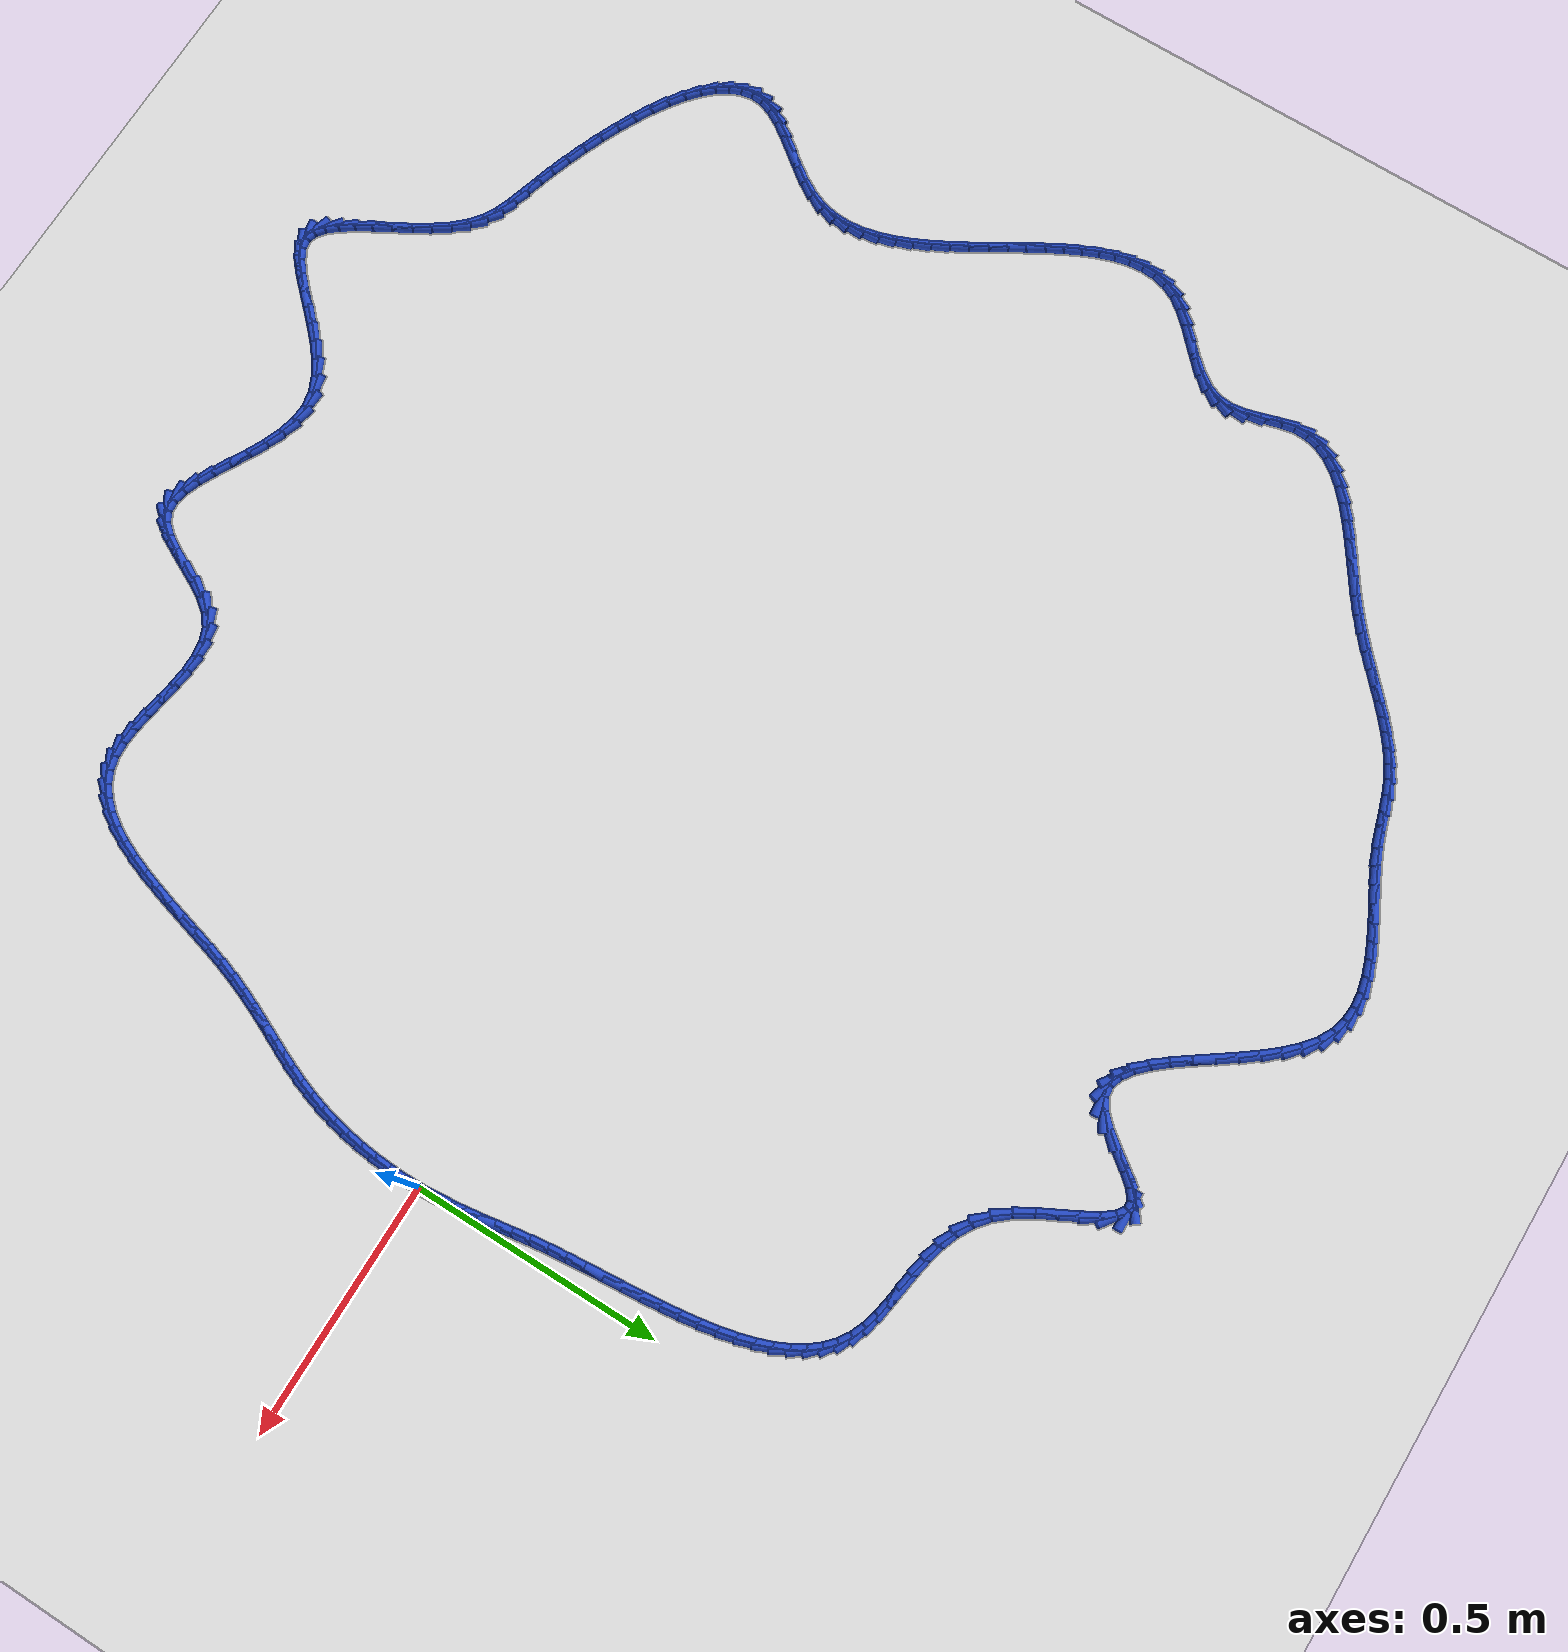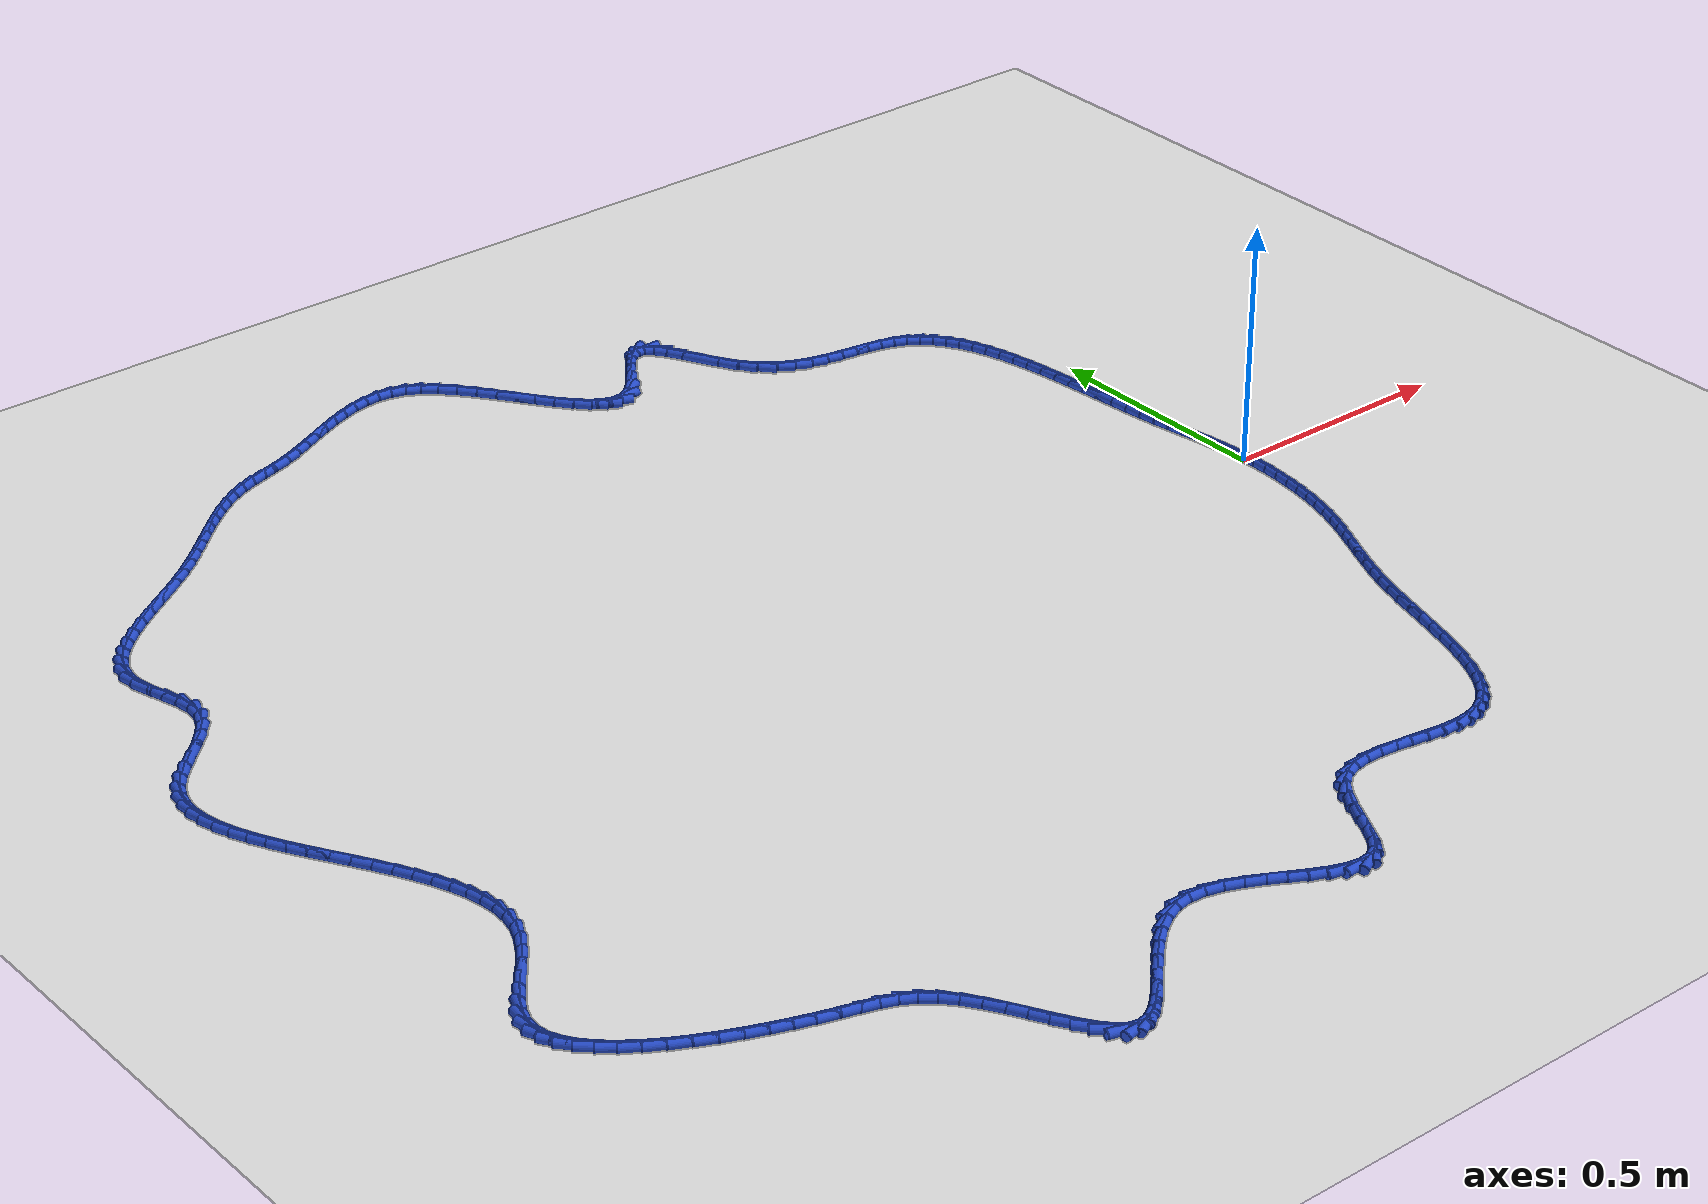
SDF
<sdf version="1.6">
 <world name="default">
  <light name="sun" type="directional">
   <pose>0 0 10 0 -0 0</pose>
   <diffuse>0.8 0.8 0.8 1</diffuse>
   <specular>0.2 0.2 0.2 1</specular>
   <attenuation>
    <range>1000</range>
    <constant>0.9</constant>
    <linear>0.01</linear>
    <quadratic>0.001</quadratic>
   </attenuation>
   <direction>-0.5 0.1 -0.9</direction>
  </light>
  <model name="ground_plane">
   <static>1</static>
   <link name="link">
    <collision name="collision">
     <geometry><plane><normal>0 0 1</normal><size>100 100</size></plane></geometry>
     <surface><friction><ode><mu>100</mu><mu2>50</mu2></ode></friction></surface>
    </collision>
    <visual name="visual">
     <cast_shadows>0</cast_shadows>
     <geometry><plane><normal>0 0 1</normal><size>100 100</size></plane></geometry>
     <material>
      <script><uri>file://media/materials/scripts/gazebo.material</uri><name>Gazebo/WhiteGlow</name></script>
     </material>
    </visual>
   </link>
  </model>
  <gravity>0 0 -9.8</gravity>
  <magnetic_field>6e-06 2.3e-05 -4.2e-05</magnetic_field>
  <atmosphere type="adiabatic"/>
  <physics name="default_physics" default="0" type="ode">
   <max_step_size>0.001</max_step_size>
   <real_time_factor>1</real_time_factor>
   <real_time_update_rate>1000</real_time_update_rate>
  </physics>
  <scene><ambient>0.4 0.4 0.4 1</ambient><background>0.7 0.7 0.7 1</background><shadows>1</shadows></scene>
  <spherical_coordinates>
   <surface_model>EARTH_WGS84</surface_model>
   <latitude_deg>0</latitude_deg>
   <longitude_deg>0</longitude_deg>
   <elevation>0</elevation>
   <heading_deg>0</heading_deg>
  </spherical_coordinates>
  <model name="line">
   <link name="link_0">
    <pose>5.204170427930421e-18 0.0 0.01 0 1.57 -1.5065319160042556</pose>
    <collision name="collision">
     <geometry><cylinder><radius>0.01</radius><length>0.08</length></cylinder></geometry>
    </collision>
    <visual name="visual">
     <material>
      <script><name>Gazebo/Blue</name><uri>file://media/materials/scripts/gazebo.material</uri></script>
     </material>
     <geometry><cylinder><radius>0.01</radius><length>0.08</length></cylinder></geometry>
    </visual>
   </link>
   <link name="link_1">
    <pose>-0.00204267366617054 0.031741687880043064 0.01 0 1.57 -1.4699507299500543</pose>
    <collision name="collision">
     <geometry><cylinder><radius>0.01</radius><length>0.08</length></cylinder></geometry>
    </collision>
    <visual name="visual">
     <material>
      <script><name>Gazebo/Blue</name><uri>file://media/materials/scripts/gazebo.material</uri></script>
     </material>
     <geometry><cylinder><radius>0.01</radius><length>0.08</length></cylinder></geometry>
    </visual>
   </link>
   <link name="link_2">
    <pose>-0.005219300440539194 0.06313473800753344 0.01 0 1.57 -1.44181646894058</pose>
    <collision name="collision">
     <geometry><cylinder><radius>0.01</radius><length>0.08</length></cylinder></geometry>
    </collision>
    <visual name="visual">
     <material>
      <script><name>Gazebo/Blue</name><uri>file://media/materials/scripts/gazebo.material</uri></script>
     </material>
     <geometry><cylinder><radius>0.01</radius><length>0.08</length></cylinder></geometry>
    </visual>
   </link>
   <link name="link_3">
    <pose>-0.009276293561994 0.09441459119313915 0.01 0 1.57 -1.422733107835847</pose>
    <collision name="collision">
     <geometry><cylinder><radius>0.01</radius><length>0.08</length></cylinder></geometry>
    </collision>
    <visual name="visual">
     <material>
      <script><name>Gazebo/Blue</name><uri>file://media/materials/scripts/gazebo.material</uri></script>
     </material>
     <geometry><cylinder><radius>0.01</radius><length>0.08</length></cylinder></geometry>
    </visual>
   </link>
   <link name="link_4">
    <pose>-0.013960066269423 0.12581668824752817 0.01 0 1.57 -1.4128963723806673</pose>
    <collision name="collision">
     <geometry><cylinder><radius>0.01</radius><length>0.08</length></cylinder></geometry>
    </collision>
    <visual name="visual">
     <material>
      <script><name>Gazebo/Blue</name><uri>file://media/materials/scripts/gazebo.material</uri></script>
     </material>
     <geometry><cylinder><radius>0.01</radius><length>0.08</length></cylinder></geometry>
    </visual>
   </link>
   <link name="link_5">
    <pose>-0.01901703180171423 0.15757646998136846 0.01 0 1.57 -1.4121378567576481</pose>
    <collision name="collision">
     <geometry><cylinder><radius>0.01</radius><length>0.08</length></cylinder></geometry>
    </collision>
    <visual name="visual">
     <material>
      <script><name>Gazebo/Blue</name><uri>file://media/materials/scripts/gazebo.material</uri></script>
     </material>
     <geometry><cylinder><radius>0.01</radius><length>0.08</length></cylinder></geometry>
    </visual>
   </link>
   <link name="link_6">
    <pose>-0.024193603397755753 0.1899293772053281 0.01 0 1.57 -1.4199802181084986</pose>
    <collision name="collision">
     <geometry><cylinder><radius>0.01</radius><length>0.08</length></cylinder></geometry>
    </collision>
    <visual name="visual">
     <material>
      <script><name>Gazebo/Blue</name><uri>file://media/materials/scripts/gazebo.material</uri></script>
     </material>
     <geometry><cylinder><radius>0.01</radius><length>0.08</length></cylinder></geometry>
    </visual>
   </link>
   <link name="link_7">
    <pose>-0.029236194296435595 0.22311085073007497 0.01 0 1.57 -1.435693346711526</pose>
    <collision name="collision">
     <geometry><cylinder><radius>0.01</radius><length>0.08</length></cylinder></geometry>
    </collision>
    <visual name="visual">
     <material>
      <script><name>Gazebo/Blue</name><uri>file://media/materials/scripts/gazebo.material</uri></script>
     </material>
     <geometry><cylinder><radius>0.01</radius><length>0.08</length></cylinder></geometry>
    </visual>
   </link>
   <link name="link_8">
    <pose>-0.0338912177366418 0.2573563313662772 0.01 0 1.57 -1.4561835001598433</pose>
    <collision name="collision">
     <geometry><cylinder><radius>0.01</radius><length>0.08</length></cylinder></geometry>
    </collision>
    <visual name="visual">
     <material>
      <script><name>Gazebo/Blue</name><uri>file://media/materials/scripts/gazebo.material</uri></script>
     </material>
     <geometry><cylinder><radius>0.01</radius><length>0.08</length></cylinder></geometry>
    </visual>
   </link>
   <link name="link_9">
    <pose>-0.03797395466479403 0.292822206277312 0.01 0 1.57 -1.4714053504873996</pose>
    <collision name="collision">
     <geometry><cylinder><radius>0.01</radius><length>0.08</length></cylinder></geometry>
    </collision>
    <visual name="visual">
     <material>
      <script><name>Gazebo/Blue</name><uri>file://media/materials/scripts/gazebo.material</uri></script>
     </material>
     <geometry><cylinder><radius>0.01</radius><length>0.08</length></cylinder></geometry>
    </visual>
   </link>
   <link name="link_10">
    <pose>-0.04161212363871337 0.32930621365133556 0.01 0 1.57 -1.4793840261193771</pose>
    <collision name="collision">
     <geometry><cylinder><radius>0.01</radius><length>0.08</length></cylinder></geometry>
    </collision>
    <visual name="visual">
     <material>
      <script><name>Gazebo/Blue</name><uri>file://media/materials/scripts/gazebo.material</uri></script>
     </material>
     <geometry><cylinder><radius>0.01</radius><length>0.08</length></cylinder></geometry>
    </visual>
   </link>
   <link name="link_11">
    <pose>-0.04502200179164849 0.36650443476592304 0.01 0 1.57 -1.4806925210956428</pose>
    <collision name="collision">
     <geometry><cylinder><radius>0.01</radius><length>0.08</length></cylinder></geometry>
    </collision>
    <visual name="visual">
     <material>
      <script><name>Gazebo/Blue</name><uri>file://media/materials/scripts/gazebo.material</uri></script>
     </material>
     <geometry><cylinder><radius>0.01</radius><length>0.08</length></cylinder></geometry>
    </visual>
   </link>
   <link name="link_12">
    <pose>-0.048419872030523205 0.4041129442710151 0.01 0 1.57 -1.4755752256892347</pose>
    <collision name="collision">
     <geometry><cylinder><radius>0.01</radius><length>0.08</length></cylinder></geometry>
    </collision>
    <visual name="visual">
     <material>
      <script><name>Gazebo/Blue</name><uri>file://media/materials/scripts/gazebo.material</uri></script>
     </material>
     <geometry><cylinder><radius>0.01</radius><length>0.08</length></cylinder></geometry>
    </visual>
   </link>
   <link name="link_13">
    <pose>-0.05202201726226119 0.44182781681655114 0.01 0 1.57 -1.4639818279687642</pose>
    <collision name="collision">
     <geometry><cylinder><radius>0.01</radius><length>0.08</length></cylinder></geometry>
    </collision>
    <visual name="visual">
     <material>
      <script><name>Gazebo/Blue</name><uri>file://media/materials/scripts/gazebo.material</uri></script>
     </material>
     <geometry><cylinder><radius>0.01</radius><length>0.08</length></cylinder></geometry>
    </visual>
   </link>
   <link name="link_14">
    <pose>-0.056044720393786183 0.4793451270524713 0.01 0 1.57 -1.445575172398241</pose>
    <collision name="collision">
     <geometry><cylinder><radius>0.01</radius><length>0.08</length></cylinder></geometry>
    </collision>
    <visual name="visual">
     <material>
      <script><name>Gazebo/Blue</name><uri>file://media/materials/scripts/gazebo.material</uri></script>
     </material>
     <geometry><cylinder><radius>0.01</radius><length>0.08</length></cylinder></geometry>
    </visual>
   </link>
   <link name="link_15">
    <pose>-0.06070426433202192 0.5163609496287158 0.01 0 1.57 -1.4197165309520097</pose>
    <collision name="collision">
     <geometry><cylinder><radius>0.01</radius><length>0.08</length></cylinder></geometry>
    </collision>
    <visual name="visual">
     <material>
      <script><name>Gazebo/Blue</name><uri>file://media/materials/scripts/gazebo.material</uri></script>
     </material>
     <geometry><cylinder><radius>0.01</radius><length>0.08</length></cylinder></geometry>
    </visual>
   </link>
   <link name="link_16">
    <pose>-0.06621693198389213 0.5525713591952244 0.01 0 1.57 -1.3854312193046547</pose>
    <collision name="collision">
     <geometry><cylinder><radius>0.01</radius><length>0.08</length></cylinder></geometry>
    </collision>
    <visual name="visual">
     <material>
      <script><name>Gazebo/Blue</name><uri>file://media/materials/scripts/gazebo.material</uri></script>
     </material>
     <geometry><cylinder><radius>0.01</radius><length>0.08</length></cylinder></geometry>
    </visual>
   </link>
   <link name="link_17">
    <pose>-0.07279900625632056 0.5876724304019372 0.01 0 1.57 -1.341359589388428</pose>
    <collision name="collision">
     <geometry><cylinder><radius>0.01</radius><length>0.08</length></cylinder></geometry>
    </collision>
    <visual name="visual">
     <material>
      <script><name>Gazebo/Blue</name><uri>file://media/materials/scripts/gazebo.material</uri></script>
     </material>
     <geometry><cylinder><radius>0.01</radius><length>0.08</length></cylinder></geometry>
    </visual>
   </link>
   <link name="link_18">
    <pose>-0.08066677005623091 0.6213602378987942 0.01 0 1.57 -1.2857063093187713</pose>
    <collision name="collision">
     <geometry><cylinder><radius>0.01</radius><length>0.08</length></cylinder></geometry>
    </collision>
    <visual name="visual">
     <material>
      <script><name>Gazebo/Blue</name><uri>file://media/materials/scripts/gazebo.material</uri></script>
     </material>
     <geometry><cylinder><radius>0.01</radius><length>0.08</length></cylinder></geometry>
    </visual>
   </link>
   <link name="link_19">
    <pose>-0.09003650629054694 0.6533308563357355 0.01 0 1.57 -1.216220381780387</pose>
    <collision name="collision">
     <geometry><cylinder><radius>0.01</radius><length>0.08</length></cylinder></geometry>
    </collision>
    <visual name="visual">
     <material>
      <script><name>Gazebo/Blue</name><uri>file://media/materials/scripts/gazebo.material</uri></script>
     </material>
     <geometry><cylinder><radius>0.01</radius><length>0.08</length></cylinder></geometry>
    </visual>
   </link>
   <link name="link_20">
    <pose>-0.10112449786619233 0.6832803603627009 0.01 0 1.57 -1.130278778096658</pose>
    <collision name="collision">
     <geometry><cylinder><radius>0.01</radius><length>0.08</length></cylinder></geometry>
    </collision>
    <visual name="visual">
     <material>
      <script><name>Gazebo/Blue</name><uri>file://media/materials/scripts/gazebo.material</uri></script>
     </material>
     <geometry><cylinder><radius>0.01</radius><length>0.08</length></cylinder></geometry>
    </visual>
   </link>
   <link name="link_21">
    <pose>-0.11414702769009089 0.7109048246296306 0.01 0 1.57 -1.025213998023638</pose>
    <collision name="collision">
     <geometry><cylinder><radius>0.01</radius><length>0.08</length></cylinder></geometry>
    </collision>
    <visual name="visual">
     <material>
      <script><name>Gazebo/Blue</name><uri>file://media/materials/scripts/gazebo.material</uri></script>
     </material>
     <geometry><cylinder><radius>0.01</radius><length>0.08</length></cylinder></geometry>
    </visual>
   </link>
   <link name="link_22">
    <pose>-0.1293203786691663 0.7359003237864643 0.01 0 1.57 -0.8990926933916177</pose>
    <collision name="collision">
     <geometry><cylinder><radius>0.01</radius><length>0.08</length></cylinder></geometry>
    </collision>
    <visual name="visual">
     <material>
      <script><name>Gazebo/Blue</name><uri>file://media/materials/scripts/gazebo.material</uri></script>
     </material>
     <geometry><cylinder><radius>0.01</radius><length>0.08</length></cylinder></geometry>
    </visual>
   </link>
   <link name="link_23">
    <pose>-0.14686083371034225 0.7579629324831424 0.01 0 1.57 -0.7520841441601266</pose>
    <collision name="collision">
     <geometry><cylinder><radius>0.01</radius><length>0.08</length></cylinder></geometry>
    </collision>
    <visual name="visual">
     <material>
      <script><name>Gazebo/Blue</name><uri>file://media/materials/scripts/gazebo.material</uri></script>
     </material>
     <geometry><cylinder><radius>0.01</radius><length>0.08</length></cylinder></geometry>
    </visual>
   </link>
   <link name="link_24">
    <pose>-0.16698467572054265 0.776788725369605 0.01 0 1.57 -0.5880844573217827</pose>
    <collision name="collision">
     <geometry><cylinder><radius>0.01</radius><length>0.08</length></cylinder></geometry>
    </collision>
    <visual name="visual">
     <material>
      <script><name>Gazebo/Blue</name><uri>file://media/materials/scripts/gazebo.material</uri></script>
     </material>
     <geometry><cylinder><radius>0.01</radius><length>0.08</length></cylinder></geometry>
    </visual>
   </link>
   <link name="link_25">
    <pose>-0.18990818760669098 0.7920737770957913 0.01 0 1.57 -0.41761652139429334</pose>
    <collision name="collision">
     <geometry><cylinder><radius>0.01</radius><length>0.08</length></cylinder></geometry>
    </collision>
    <visual name="visual">
     <material>
      <script><name>Gazebo/Blue</name><uri>file://media/materials/scripts/gazebo.material</uri></script>
     </material>
     <geometry><cylinder><radius>0.01</radius><length>0.08</length></cylinder></geometry>
    </visual>
   </link>
   <link name="link_26">
    <pose>-0.2158151067154066 0.8035691116116817 0.01 0 1.57 -0.2802086820223118</pose>
    <collision name="collision">
     <geometry><cylinder><radius>0.01</radius><length>0.08</length></cylinder></geometry>
    </collision>
    <visual name="visual">
     <material>
      <script><name>Gazebo/Blue</name><uri>file://media/materials/scripts/gazebo.material</uri></script>
     </material>
     <geometry><cylinder><radius>0.01</radius><length>0.08</length></cylinder></geometry>
    </visual>
   </link>
   <link name="link_27">
    <pose>-0.2444285293893745 0.8118034903066735 0.01 0 1.57 -0.19547326191610667</pose>
    <collision name="collision">
     <geometry><cylinder><radius>0.01</radius><length>0.08</length></cylinder></geometry>
    </collision>
    <visual name="visual">
     <material>
      <script><name>Gazebo/Blue</name><uri>file://media/materials/scripts/gazebo.material</uri></script>
     </material>
     <geometry><cylinder><radius>0.01</radius><length>0.08</length></cylinder></geometry>
    </visual>
   </link>
   <link name="link_28">
    <pose>-0.27512995467354223 0.8178824208984032 0.01 0 1.57 -0.15551766078282228</pose>
    <collision name="collision">
     <geometry><cylinder><radius>0.01</radius><length>0.08</length></cylinder></geometry>
    </collision>
    <visual name="visual">
     <material>
      <script><name>Gazebo/Blue</name><uri>file://media/materials/scripts/gazebo.material</uri></script>
     </material>
     <geometry><cylinder><radius>0.01</radius><length>0.08</length></cylinder></geometry>
    </visual>
   </link>
   <link name="link_29">
    <pose>-0.3072928139791497 0.822925032342581 0.01 0 1.57 -0.15409512898195696</pose>
    <collision name="collision">
     <geometry><cylinder><radius>0.01</radius><length>0.08</length></cylinder></geometry>
    </collision>
    <visual name="visual">
     <material>
      <script><name>Gazebo/Blue</name><uri>file://media/materials/scripts/gazebo.material</uri></script>
     </material>
     <geometry><cylinder><radius>0.01</radius><length>0.08</length></cylinder></geometry>
    </visual>
   </link>
   <link name="link_30">
    <pose>-0.34029053871743736 0.8280504535949176 0.01 0 1.57 -0.18829135239080647</pose>
    <collision name="collision">
     <geometry><cylinder><radius>0.01</radius><length>0.08</length></cylinder></geometry>
    </collision>
    <visual name="visual">
     <material>
      <script><name>Gazebo/Blue</name><uri>file://media/materials/scripts/gazebo.material</uri></script>
     </material>
     <geometry><cylinder><radius>0.01</radius><length>0.08</length></cylinder></geometry>
    </visual>
   </link>
   <link name="link_31">
    <pose>-0.3734965602996452 0.8343778136111235 0.01 0 1.57 -0.2578961742604394</pose>
    <collision name="collision">
     <geometry><cylinder><radius>0.01</radius><length>0.08</length></cylinder></geometry>
    </collision>
    <visual name="visual">
     <material>
      <script><name>Gazebo/Blue</name><uri>file://media/materials/scripts/gazebo.material</uri></script>
     </material>
     <geometry><cylinder><radius>0.01</radius><length>0.08</length></cylinder></geometry>
    </visual>
   </link>
   <link name="link_32">
    <pose>-0.4062843101370137 0.8430262413469096 0.01 0 1.57 -0.3638713155943997</pose>
    <collision name="collision">
     <geometry><cylinder><radius>0.01</radius><length>0.08</length></cylinder></geometry>
    </collision>
    <visual name="visual">
     <material>
      <script><name>Gazebo/Blue</name><uri>file://media/materials/scripts/gazebo.material</uri></script>
     </material>
     <geometry><cylinder><radius>0.01</radius><length>0.08</length></cylinder></geometry>
    </visual>
   </link>
   <link name="link_33">
    <pose>-0.43802721964078284 0.8551148657579862 0.01 0 1.57 -0.5056122737413987</pose>
    <collision name="collision">
     <geometry><cylinder><radius>0.01</radius><length>0.08</length></cylinder></geometry>
    </collision>
    <visual name="visual">
     <material>
      <script><name>Gazebo/Blue</name><uri>file://media/materials/scripts/gazebo.material</uri></script>
     </material>
     <geometry><cylinder><radius>0.01</radius><length>0.08</length></cylinder></geometry>
    </visual>
   </link>
   <link name="link_34">
    <pose>-0.4680987202221928 0.8717628158000641 0.01 0 1.57 -0.6770984924806728</pose>
    <collision name="collision">
     <geometry><cylinder><radius>0.01</radius><length>0.08</length></cylinder></geometry>
    </collision>
    <visual name="visual">
     <material>
      <script><name>Gazebo/Blue</name><uri>file://media/materials/scripts/gazebo.material</uri></script>
     </material>
     <geometry><cylinder><radius>0.01</radius><length>0.08</length></cylinder></geometry>
    </visual>
   </link>
   <link name="link_35">
    <pose>-0.4958722432924839 0.894089220428854 0.01 0 1.57 -0.8607451220738295</pose>
    <collision name="collision">
     <geometry><cylinder><radius>0.01</radius><length>0.08</length></cylinder></geometry>
    </collision>
    <visual name="visual">
     <material>
      <script><name>Gazebo/Blue</name><uri>file://media/materials/scripts/gazebo.material</uri></script>
     </material>
     <geometry><cylinder><radius>0.01</radius><length>0.08</length></cylinder></geometry>
    </visual>
   </link>
   <link name="link_36">
    <pose>-0.5207690216685414 0.9230518375067694 0.01 0 1.57 -0.9967159110644279</pose>
    <collision name="collision">
     <geometry><cylinder><radius>0.01</radius><length>0.08</length></cylinder></geometry>
    </collision>
    <visual name="visual">
     <material>
      <script><name>Gazebo/Blue</name><uri>file://media/materials/scripts/gazebo.material</uri></script>
     </material>
     <geometry><cylinder><radius>0.01</radius><length>0.08</length></cylinder></geometry>
    </visual>
   </link>
   <link name="link_37">
    <pose>-0.5429018199149612 0.9572739070578841 0.01 0 1.57 -1.067725159132845</pose>
    <collision name="collision">
     <geometry><cylinder><radius>0.01</radius><length>0.08</length></cylinder></geometry>
    </collision>
    <visual name="visual">
     <material>
      <script><name>Gazebo/Blue</name><uri>file://media/materials/scripts/gazebo.material</uri></script>
     </material>
     <geometry><cylinder><radius>0.01</radius><length>0.08</length></cylinder></geometry>
    </visual>
   </link>
   <link name="link_38">
    <pose>-0.5629038690540661 0.9936216445967639 0.01 0 1.57 -1.0876493455513092</pose>
    <collision name="collision">
     <geometry><cylinder><radius>0.01</radius><length>0.08</length></cylinder></geometry>
    </collision>
    <visual name="visual">
     <material>
      <script><name>Gazebo/Blue</name><uri>file://media/materials/scripts/gazebo.material</uri></script>
     </material>
     <geometry><cylinder><radius>0.01</radius><length>0.08</length></cylinder></geometry>
    </visual>
   </link>
   <link name="link_39">
    <pose>-0.5814211199564625 1.0289183251470821 0.01 0 1.57 -1.0534780282573086</pose>
    <collision name="collision">
     <geometry><cylinder><radius>0.01</radius><length>0.08</length></cylinder></geometry>
    </collision>
    <visual name="visual">
     <material>
      <script><name>Gazebo/Blue</name><uri>file://media/materials/scripts/gazebo.material</uri></script>
     </material>
     <geometry><cylinder><radius>0.01</radius><length>0.08</length></cylinder></geometry>
    </visual>
   </link>
   <link name="link_40">
    <pose>-0.5990995234927567 1.0599872237325112 0.01 0 1.57 -0.9344402093378655</pose>
    <collision name="collision">
     <geometry><cylinder><radius>0.01</radius><length>0.08</length></cylinder></geometry>
    </collision>
    <visual name="visual">
     <material>
      <script><name>Gazebo/Blue</name><uri>file://media/materials/scripts/gazebo.material</uri></script>
     </material>
     <geometry><cylinder><radius>0.01</radius><length>0.08</length></cylinder></geometry>
    </visual>
   </link>
   <link name="link_41">
    <pose>-0.616585030533555 1.083651615376723 0.01 0 1.57 -0.6301415831349697</pose>
    <collision name="collision">
     <geometry><cylinder><radius>0.01</radius><length>0.08</length></cylinder></geometry>
    </collision>
    <visual name="visual">
     <material>
      <script><name>Gazebo/Blue</name><uri>file://media/materials/scripts/gazebo.material</uri></script>
     </material>
     <geometry><cylinder><radius>0.01</radius><length>0.08</length></cylinder></geometry>
    </visual>
   </link>
   <link name="link_42">
    <pose>-0.634523591949463 1.0967347751033896 0.01 0 1.57 0.03483097757005292</pose>
    <collision name="collision">
     <geometry><cylinder><radius>0.01</radius><length>0.08</length></cylinder></geometry>
    </collision>
    <visual name="visual">
     <material>
      <script><name>Gazebo/Blue</name><uri>file://media/materials/scripts/gazebo.material</uri></script>
     </material>
     <geometry><cylinder><radius>0.01</radius><length>0.08</length></cylinder></geometry>
    </visual>
   </link>
   <link name="link_43">
    <pose>-0.6535598181863246 1.096071456467224 0.01 0 1.57 0.6375500496984747</pose>
    <collision name="collision">
     <geometry><cylinder><radius>0.01</radius><length>0.08</length></cylinder></geometry>
    </collision>
    <visual name="visual">
     <material>
      <script><name>Gazebo/Blue</name><uri>file://media/materials/scripts/gazebo.material</uri></script>
     </material>
     <geometry><cylinder><radius>0.01</radius><length>0.08</length></cylinder></geometry>
    </visual>
   </link>
   <link name="link_44">
    <pose>-0.6740591903004785 1.0808866966489687 0.01 0 1.57 0.8591065303904463</pose>
    <collision name="collision">
     <geometry><cylinder><radius>0.01</radius><length>0.08</length></cylinder></geometry>
    </collision>
    <visual name="visual">
     <material>
      <script><name>Gazebo/Blue</name><uri>file://media/materials/scripts/gazebo.material</uri></script>
     </material>
     <geometry><cylinder><radius>0.01</radius><length>0.08</length></cylinder></geometry>
    </visual>
   </link>
   <link name="link_45">
    <pose>-0.6957668722198219 1.0557175276633386 0.01 0 1.57 0.9240536739080228</pose>
    <collision name="collision">
     <geometry><cylinder><radius>0.01</radius><length>0.08</length></cylinder></geometry>
    </collision>
    <visual name="visual">
     <material>
      <script><name>Gazebo/Blue</name><uri>file://media/materials/scripts/gazebo.material</uri></script>
     </material>
     <geometry><cylinder><radius>0.01</radius><length>0.08</length></cylinder></geometry>
    </visual>
   </link>
   <link name="link_46">
    <pose>-0.7183444744359614 1.0258164791335898 0.01 0 1.57 0.9043109877833828</pose>
    <collision name="collision">
     <geometry><cylinder><radius>0.01</radius><length>0.08</length></cylinder></geometry>
    </collision>
    <visual name="visual">
     <material>
      <script><name>Gazebo/Blue</name><uri>file://media/materials/scripts/gazebo.material</uri></script>
     </material>
     <geometry><cylinder><radius>0.01</radius><length>0.08</length></cylinder></geometry>
    </visual>
   </link>
   <link name="link_47">
    <pose>-0.7414536074405028 0.9964360806829778 0.01 0 1.57 0.7918987701724323</pose>
    <collision name="collision">
     <geometry><cylinder><radius>0.01</radius><length>0.08</length></cylinder></geometry>
    </collision>
    <visual name="visual">
     <material>
      <script><name>Gazebo/Blue</name><uri>file://media/materials/scripts/gazebo.material</uri></script>
     </material>
     <geometry><cylinder><radius>0.01</radius><length>0.08</length></cylinder></geometry>
    </visual>
   </link>
   <link name="link_48">
    <pose>-0.764755881725053 0.9728288619347593 0.01 0 1.57 0.5141964157422834</pose>
    <collision name="collision">
     <geometry><cylinder><radius>0.01</radius><length>0.08</length></cylinder></geometry>
    </collision>
    <visual name="visual">
     <material>
      <script><name>Gazebo/Blue</name><uri>file://media/materials/scripts/gazebo.material</uri></script>
     </material>
     <geometry><cylinder><radius>0.01</radius><length>0.08</length></cylinder></geometry>
    </visual>
   </link>
   <link name="link_49">
    <pose>-0.787945919766768 0.9597292475000573 0.01 0 1.57 0.08817299291202654</pose>
    <collision name="collision">
     <geometry><cylinder><radius>0.01</radius><length>0.08</length></cylinder></geometry>
    </collision>
    <visual name="visual">
     <material>
      <script><name>Gazebo/Blue</name><uri>file://media/materials/scripts/gazebo.material</uri></script>
     </material>
     <geometry><cylinder><radius>0.01</radius><length>0.08</length></cylinder></geometry>
    </visual>
   </link>
   <link name="link_50">
    <pose>-0.8109846220027547 0.9576925754136051 0.01 0 1.57 -0.3179568789169306</pose>
    <collision name="collision">
     <geometry><cylinder><radius>0.01</radius><length>0.08</length></cylinder></geometry>
    </collision>
    <visual name="visual">
     <material>
      <script><name>Gazebo/Blue</name><uri>file://media/materials/scripts/gazebo.material</uri></script>
     </material>
     <geometry><cylinder><radius>0.01</radius><length>0.08</length></cylinder></geometry>
    </visual>
   </link>
   <link name="link_51">
    <pose>-0.8339615560401962 0.9652548230263346 0.01 0 1.57 -0.5983718168953571</pose>
    <collision name="collision">
     <geometry><cylinder><radius>0.01</radius><length>0.08</length></cylinder></geometry>
    </collision>
    <visual name="visual">
     <material>
      <script><name>Gazebo/Blue</name><uri>file://media/materials/scripts/gazebo.material</uri></script>
     </material>
     <geometry><cylinder><radius>0.01</radius><length>0.08</length></cylinder></geometry>
    </visual>
   </link>
   <link name="link_52">
    <pose>-0.856967125181823 0.9809388519057919 0.01 0 1.57 -0.767888876762374</pose>
    <collision name="collision">
     <geometry><cylinder><radius>0.01</radius><length>0.08</length></cylinder></geometry>
    </collision>
    <visual name="visual">
     <material>
      <script><name>Gazebo/Blue</name><uri>file://media/materials/scripts/gazebo.material</uri></script>
     </material>
     <geometry><cylinder><radius>0.01</radius><length>0.08</length></cylinder></geometry>
    </visual>
   </link>
   <link name="link_53">
    <pose>-0.880091732730365 1.0032675236195232 0.01 0 1.57 -0.8670988046629311</pose>
    <collision name="collision">
     <geometry><cylinder><radius>0.01</radius><length>0.08</length></cylinder></geometry>
    </collision>
    <visual name="visual">
     <material>
      <script><name>Gazebo/Blue</name><uri>file://media/materials/scripts/gazebo.material</uri></script>
     </material>
     <geometry><cylinder><radius>0.01</radius><length>0.08</length></cylinder></geometry>
    </visual>
   </link>
   <link name="link_54">
    <pose>-0.9034257819885528 1.0307636997350755 0.01 0 1.57 -0.9223069560454744</pose>
    <collision name="collision">
     <geometry><cylinder><radius>0.01</radius><length>0.08</length></cylinder></geometry>
    </collision>
    <visual name="visual">
     <material>
      <script><name>Gazebo/Blue</name><uri>file://media/materials/scripts/gazebo.material</uri></script>
     </material>
     <geometry><cylinder><radius>0.01</radius><length>0.08</length></cylinder></geometry>
    </visual>
   </link>
   <link name="link_55">
    <pose>-0.9270596762591161 1.061950241819995 0.01 0 1.57 -0.9472405888301</pose>
    <collision name="collision">
     <geometry><cylinder><radius>0.01</radius><length>0.08</length></cylinder></geometry>
    </collision>
    <visual name="visual">
     <material>
      <script><name>Gazebo/Blue</name><uri>file://media/materials/scripts/gazebo.material</uri></script>
     </material>
     <geometry><cylinder><radius>0.01</radius><length>0.08</length></cylinder></geometry>
    </visual>
   </link>
   <link name="link_56">
    <pose>-0.9510838188447861 1.0953500114418289 0.01 0 1.57 -0.9481835674321908</pose>
    <collision name="collision">
     <geometry><cylinder><radius>0.01</radius><length>0.08</length></cylinder></geometry>
    </collision>
    <visual name="visual">
     <material>
      <script><name>Gazebo/Blue</name><uri>file://media/materials/scripts/gazebo.material</uri></script>
     </material>
     <geometry><cylinder><radius>0.01</radius><length>0.08</length></cylinder></geometry>
    </visual>
   </link>
   <link name="link_57">
    <pose>-0.975588613048292 1.129485870168123 0.01 0 1.57 -0.9267254650190411</pose>
    <collision name="collision">
     <geometry><cylinder><radius>0.01</radius><length>0.08</length></cylinder></geometry>
    </collision>
    <visual name="visual">
     <material>
      <script><name>Gazebo/Blue</name><uri>file://media/materials/scripts/gazebo.material</uri></script>
     </material>
     <geometry><cylinder><radius>0.01</radius><length>0.08</length></cylinder></geometry>
    </visual>
   </link>
   <link name="link_58">
    <pose>-1.0006644621723648 1.162880679566424 0.01 0 1.57 -0.8806796530365831</pose>
    <collision name="collision">
     <geometry><cylinder><radius>0.01</radius><length>0.08</length></cylinder></geometry>
    </collision>
    <visual name="visual">
     <material>
      <script><name>Gazebo/Blue</name><uri>file://media/materials/scripts/gazebo.material</uri></script>
     </material>
     <geometry><cylinder><radius>0.01</radius><length>0.08</length></cylinder></geometry>
    </visual>
   </link>
   <link name="link_59">
    <pose>-1.0264017695197345 1.1940573012042786 0.01 0 1.57 -0.8037788620176313</pose>
    <collision name="collision">
     <geometry><cylinder><radius>0.01</radius><length>0.08</length></cylinder></geometry>
    </collision>
    <visual name="visual">
     <material>
      <script><name>Gazebo/Blue</name><uri>file://media/materials/scripts/gazebo.material</uri></script>
     </material>
     <geometry><cylinder><radius>0.01</radius><length>0.08</length></cylinder></geometry>
    </visual>
   </link>
   <link name="link_60">
    <pose>-1.052890938393131 1.2215385966492331 0.01 0 1.57 -0.6845613127759893</pose>
    <collision name="collision">
     <geometry><cylinder><radius>0.01</radius><length>0.08</length></cylinder></geometry>
    </collision>
    <visual name="visual">
     <material>
      <script><name>Gazebo/Blue</name><uri>file://media/materials/scripts/gazebo.material</uri></script>
     </material>
     <geometry><cylinder><radius>0.01</radius><length>0.08</length></cylinder></geometry>
    </visual>
   </link>
   <link name="link_61">
    <pose>-1.080222372095285 1.243847427468834 0.01 0 1.57 -0.5073778969088185</pose>
    <collision name="collision">
     <geometry><cylinder><radius>0.01</radius><length>0.08</length></cylinder></geometry>
    </collision>
    <visual name="visual">
     <material>
      <script><name>Gazebo/Blue</name><uri>file://media/materials/scripts/gazebo.material</uri></script>
     </material>
     <geometry><cylinder><radius>0.01</radius><length>0.08</length></cylinder></geometry>
    </visual>
   </link>
   <link name="link_62">
    <pose>-1.1084821198815134 1.259557621418291 0.01 0 1.57 -0.29339753956743103</pose>
    <collision name="collision">
     <geometry><cylinder><radius>0.01</radius><length>0.08</length></cylinder></geometry>
    </collision>
    <visual name="visual">
     <material>
      <script><name>Gazebo/Blue</name><uri>file://media/materials/scripts/gazebo.material</uri></script>
     </material>
     <geometry><cylinder><radius>0.01</radius><length>0.08</length></cylinder></geometry>
    </visual>
   </link>
   <link name="link_63">
    <pose>-1.1376597244283624 1.2683726614763453 0.01 0 1.57 -0.09077441908600027</pose>
    <collision name="collision">
     <geometry><cylinder><radius>0.01</radius><length>0.08</length></cylinder></geometry>
    </collision>
    <visual name="visual">
     <material>
      <script><name>Gazebo/Blue</name><uri>file://media/materials/scripts/gazebo.material</uri></script>
     </material>
     <geometry><cylinder><radius>0.01</radius><length>0.08</length></cylinder></geometry>
    </visual>
   </link>
   <link name="link_64">
    <pose>-1.1676501999012348 1.2711025316266058 0.01 0 1.57 0.08123570845947972</pose>
    <collision name="collision">
     <geometry><cylinder><radius>0.01</radius><length>0.08</length></cylinder></geometry>
    </collision>
    <visual name="visual">
     <material>
      <script><name>Gazebo/Blue</name><uri>file://media/materials/scripts/gazebo.material</uri></script>
     </material>
     <geometry><cylinder><radius>0.01</radius><length>0.08</length></cylinder></geometry>
    </visual>
   </link>
   <link name="link_65">
    <pose>-1.1983446020848367 1.2686035505739883 0.01 0 1.57 0.21617985789622715</pose>
    <collision name="collision">
     <geometry><cylinder><radius>0.01</radius><length>0.08</length></cylinder></geometry>
    </collision>
    <visual name="visual">
     <material>
      <script><name>Gazebo/Blue</name><uri>file://media/materials/scripts/gazebo.material</uri></script>
     </material>
     <geometry><cylinder><radius>0.01</radius><length>0.08</length></cylinder></geometry>
    </visual>
   </link>
   <link name="link_66">
    <pose>-1.2296339867638744 1.2617320370234093 0.01 0 1.57 0.31595913504622336</pose>
    <collision name="collision">
     <geometry><cylinder><radius>0.01</radius><length>0.08</length></cylinder></geometry>
    </collision>
    <visual name="visual">
     <material>
      <script><name>Gazebo/Blue</name><uri>file://media/materials/scripts/gazebo.material</uri></script>
     </material>
     <geometry><cylinder><radius>0.01</radius><length>0.08</length></cylinder></geometry>
    </visual>
   </link>
   <link name="link_67">
    <pose>-1.2614094097230528 1.2513443096797845 0.01 0 1.57 0.385499854535347</pose>
    <collision name="collision">
     <geometry><cylinder><radius>0.01</radius><length>0.08</length></cylinder></geometry>
    </collision>
    <visual name="visual">
     <material>
      <script><name>Gazebo/Blue</name><uri>file://media/materials/scripts/gazebo.material</uri></script>
     </material>
     <geometry><cylinder><radius>0.01</radius><length>0.08</length></cylinder></geometry>
    </visual>
   </link>
   <link name="link_68">
    <pose>-1.2935619267470784 1.23829668724803 0.01 0 1.57 0.42955136815241934</pose>
    <collision name="collision">
     <geometry><cylinder><radius>0.01</radius><length>0.08</length></cylinder></geometry>
    </collision>
    <visual name="visual">
     <material>
      <script><name>Gazebo/Blue</name><uri>file://media/materials/scripts/gazebo.material</uri></script>
     </material>
     <geometry><cylinder><radius>0.01</radius><length>0.08</length></cylinder></geometry>
    </visual>
   </link>
   <link name="link_69">
    <pose>-1.3259825936206564 1.2234454884330612 0.01 0 1.57 0.4515066374205772</pose>
    <collision name="collision">
     <geometry><cylinder><radius>0.01</radius><length>0.08</length></cylinder></geometry>
    </collision>
    <visual name="visual">
     <material>
      <script><name>Gazebo/Blue</name><uri>file://media/materials/scripts/gazebo.material</uri></script>
     </material>
     <geometry><cylinder><radius>0.01</radius><length>0.08</length></cylinder></geometry>
    </visual>
   </link>
   <link name="link_70">
    <pose>-1.3585624661284939 1.2076470319397947 0.01 0 1.57 0.4531569707485363</pose>
    <collision name="collision">
     <geometry><cylinder><radius>0.01</radius><length>0.08</length></cylinder></geometry>
    </collision>
    <visual name="visual">
     <material>
      <script><name>Gazebo/Blue</name><uri>file://media/materials/scripts/gazebo.material</uri></script>
     </material>
     <geometry><cylinder><radius>0.01</radius><length>0.08</length></cylinder></geometry>
    </visual>
   </link>
   <link name="link_71">
    <pose>-1.3911926000552954 1.1917576364731464 0.01 0 1.57 0.43470952182659994</pose>
    <collision name="collision">
     <geometry><cylinder><radius>0.01</radius><length>0.08</length></cylinder></geometry>
    </collision>
    <visual name="visual">
     <material>
      <script><name>Gazebo/Blue</name><uri>file://media/materials/scripts/gazebo.material</uri></script>
     </material>
     <geometry><cylinder><radius>0.01</radius><length>0.08</length></cylinder></geometry>
    </visual>
   </link>
   <link name="link_72">
    <pose>-1.423764051185767 1.1766336207380315 0.01 0 1.57 0.39481015519320395</pose>
    <collision name="collision">
     <geometry><cylinder><radius>0.01</radius><length>0.08</length></cylinder></geometry>
    </collision>
    <visual name="visual">
     <material>
      <script><name>Gazebo/Blue</name><uri>file://media/materials/scripts/gazebo.material</uri></script>
     </material>
     <geometry><cylinder><radius>0.01</radius><length>0.08</length></cylinder></geometry>
    </visual>
   </link>
   <link name="link_73">
    <pose>-1.4561678753046148 1.1631313034393664 0.01 0 1.57 0.33446690330024514</pose>
    <collision name="collision">
     <geometry><cylinder><radius>0.01</radius><length>0.08</length></cylinder></geometry>
    </collision>
    <visual name="visual">
     <material>
      <script><name>Gazebo/Blue</name><uri>file://media/materials/scripts/gazebo.material</uri></script>
     </material>
     <geometry><cylinder><radius>0.01</radius><length>0.08</length></cylinder></geometry>
    </visual>
   </link>
   <link name="link_74">
    <pose>-1.4882762902487077 1.151972873930615 0.01 0 1.57 0.29505179756440403</pose>
    <collision name="collision">
     <geometry><cylinder><radius>0.01</radius><length>0.08</length></cylinder></geometry>
    </collision>
    <visual name="visual">
     <material>
      <script><name>Gazebo/Blue</name><uri>file://media/materials/scripts/gazebo.material</uri></script>
     </material>
     <geometry><cylinder><radius>0.01</radius><length>0.08</length></cylinder></geometry>
    </visual>
   </link>
   <link name="link_75">
    <pose>-1.5197544165003738 1.1424059536297142 0.01 0 1.57 0.3072310267096425</pose>
    <collision name="collision">
     <geometry><cylinder><radius>0.01</radius><length>0.08</length></cylinder></geometry>
    </collision>
    <visual name="visual">
     <material>
      <script><name>Gazebo/Blue</name><uri>file://media/materials/scripts/gazebo.material</uri></script>
     </material>
     <geometry><cylinder><radius>0.01</radius><length>0.08</length></cylinder></geometry>
    </visual>
   </link>
   <link name="link_76">
    <pose>-1.5501392023874183 1.1327655566945654 0.01 0 1.57 0.375468880756981</pose>
    <collision name="collision">
     <geometry><cylinder><radius>0.01</radius><length>0.08</length></cylinder></geometry>
    </collision>
    <visual name="visual">
     <material>
      <script><name>Gazebo/Blue</name><uri>file://media/materials/scripts/gazebo.material</uri></script>
     </material>
     <geometry><cylinder><radius>0.01</radius><length>0.08</length></cylinder></geometry>
    </visual>
   </link>
   <link name="link_77">
    <pose>-1.5789762599097072 1.1213989054660052 0.01 0 1.57 0.4720575145508451</pose>
    <collision name="collision">
     <geometry><cylinder><radius>0.01</radius><length>0.08</length></cylinder></geometry>
    </collision>
    <visual name="visual">
     <material>
      <script><name>Gazebo/Blue</name><uri>file://media/materials/scripts/gazebo.material</uri></script>
     </material>
     <geometry><cylinder><radius>0.01</radius><length>0.08</length></cylinder></geometry>
    </visual>
   </link>
   <link name="link_78">
    <pose>-1.6061655389184002 1.1075172281284862 0.01 0 1.57 0.5576869719665066</pose>
    <collision name="collision">
     <geometry><cylinder><radius>0.01</radius><length>0.08</length></cylinder></geometry>
    </collision>
    <visual name="visual">
     <material>
      <script><name>Gazebo/Blue</name><uri>file://media/materials/scripts/gazebo.material</uri></script>
     </material>
     <geometry><cylinder><radius>0.01</radius><length>0.08</length></cylinder></geometry>
    </visual>
   </link>
   <link name="link_79">
    <pose>-1.632037030401036 1.0913803511278857 0.01 0 1.57 0.6275628884111416</pose>
    <collision name="collision">
     <geometry><cylinder><radius>0.01</radius><length>0.08</length></cylinder></geometry>
    </collision>
    <visual name="visual">
     <material>
      <script><name>Gazebo/Blue</name><uri>file://media/materials/scripts/gazebo.material</uri></script>
     </material>
     <geometry><cylinder><radius>0.01</radius><length>0.08</length></cylinder></geometry>
    </visual>
   </link>
   <link name="link_80">
    <pose>-1.65694661246185 1.07331122320994 0.01 0 1.57 0.680623803004864</pose>
    <collision name="collision">
     <geometry><cylinder><radius>0.01</radius><length>0.08</length></cylinder></geometry>
    </collision>
    <visual name="visual">
     <material>
      <script><name>Gazebo/Blue</name><uri>file://media/materials/scripts/gazebo.material</uri></script>
     </material>
     <geometry><cylinder><radius>0.01</radius><length>0.08</length></cylinder></geometry>
    </visual>
   </link>
   <link name="link_81">
    <pose>-1.6812501632050776 1.053632793120384 0.01 0 1.57 0.7168973606551147</pose>
    <collision name="collision">
     <geometry><cylinder><radius>0.01</radius><length>0.08</length></cylinder></geometry>
    </collision>
    <visual name="visual">
     <material>
      <script><name>Gazebo/Blue</name><uri>file://media/materials/scripts/gazebo.material</uri></script>
     </material>
     <geometry><cylinder><radius>0.01</radius><length>0.08</length></cylinder></geometry>
    </visual>
   </link>
   <link name="link_82">
    <pose>-1.7053035607349547 1.0326680096049548 0.01 0 1.57 0.7370292278490008</pose>
    <collision name="collision">
     <geometry><cylinder><radius>0.01</radius><length>0.08</length></cylinder></geometry>
    </collision>
    <visual name="visual">
     <material>
      <script><name>Gazebo/Blue</name><uri>file://media/materials/scripts/gazebo.material</uri></script>
     </material>
     <geometry><cylinder><radius>0.01</radius><length>0.08</length></cylinder></geometry>
    </visual>
   </link>
   <link name="link_83">
    <pose>-1.7294626831557167 1.0107398214093875 0.01 0 1.57 0.7419394512219598</pose>
    <collision name="collision">
     <geometry><cylinder><radius>0.01</radius><length>0.08</length></cylinder></geometry>
    </collision>
    <visual name="visual">
     <material>
      <script><name>Gazebo/Blue</name><uri>file://media/materials/scripts/gazebo.material</uri></script>
     </material>
     <geometry><cylinder><radius>0.01</radius><length>0.08</length></cylinder></geometry>
    </visual>
   </link>
   <link name="link_84">
    <pose>-1.7540834085715986 0.988171177279418 0.01 0 1.57 0.7326362289257992</pose>
    <collision name="collision">
     <geometry><cylinder><radius>0.01</radius><length>0.08</length></cylinder></geometry>
    </collision>
    <visual name="visual">
     <material>
      <script><name>Gazebo/Blue</name><uri>file://media/materials/scripts/gazebo.material</uri></script>
     </material>
     <geometry><cylinder><radius>0.01</radius><length>0.08</length></cylinder></geometry>
    </visual>
   </link>
   <link name="link_85">
    <pose>-1.7795216150868376 0.9652850259607826 0.01 0 1.57 0.7101578756560705</pose>
    <collision name="collision">
     <geometry><cylinder><radius>0.01</radius><length>0.08</length></cylinder></geometry>
    </collision>
    <visual name="visual">
     <material>
      <script><name>Gazebo/Blue</name><uri>file://media/materials/scripts/gazebo.material</uri></script>
     </material>
     <geometry><cylinder><radius>0.01</radius><length>0.08</length></cylinder></geometry>
    </visual>
   </link>
   <link name="link_86">
    <pose>-1.8061331808056669 0.9424043161992168 0.01 0 1.57 0.6756000748261549</pose>
    <collision name="collision">
     <geometry><cylinder><radius>0.01</radius><length>0.08</length></cylinder></geometry>
    </collision>
    <visual name="visual">
     <material>
      <script><name>Gazebo/Blue</name><uri>file://media/materials/scripts/gazebo.material</uri></script>
     </material>
     <geometry><cylinder><radius>0.01</radius><length>0.08</length></cylinder></geometry>
    </visual>
   </link>
   <link name="link_87">
    <pose>-1.8342739838323234 0.9198519967404569 0.01 0 1.57 0.6336502863869227</pose>
    <collision name="collision">
     <geometry><cylinder><radius>0.01</radius><length>0.08</length></cylinder></geometry>
    </collision>
    <visual name="visual">
     <material>
      <script><name>Gazebo/Blue</name><uri>file://media/materials/scripts/gazebo.material</uri></script>
     </material>
     <geometry><cylinder><radius>0.01</radius><length>0.08</length></cylinder></geometry>
    </visual>
   </link>
   <link name="link_88">
    <pose>-1.8641692843395268 0.8978873071239974 0.01 0 1.57 0.604044374921689</pose>
    <collision name="collision">
     <geometry><cylinder><radius>0.01</radius><length>0.08</length></cylinder></geometry>
    </collision>
    <visual name="visual">
     <material>
      <script><name>Gazebo/Blue</name><uri>file://media/materials/scripts/gazebo.material</uri></script>
     </material>
     <geometry><cylinder><radius>0.01</radius><length>0.08</length></cylinder></geometry>
    </visual>
   </link>
   <link name="link_89">
    <pose>-1.8952981829738225 0.8764055458087319 0.01 0 1.57 0.5919644068887063</pose>
    <collision name="collision">
     <geometry><cylinder><radius>0.01</radius><length>0.08</length></cylinder></geometry>
    </collision>
    <visual name="visual">
     <material>
      <script><name>Gazebo/Blue</name><uri>file://media/materials/scripts/gazebo.material</uri></script>
     </material>
     <geometry><cylinder><radius>0.01</radius><length>0.08</length></cylinder></geometry>
    </visual>
   </link>
   <link name="link_90">
    <pose>-1.9268752493928818 0.8551729856356188 0.01 0 1.57 0.5966157131276605</pose>
    <collision name="collision">
     <geometry><cylinder><radius>0.01</radius><length>0.08</length></cylinder></geometry>
    </collision>
    <visual name="visual">
     <material>
      <script><name>Gazebo/Blue</name><uri>file://media/materials/scripts/gazebo.material</uri></script>
     </material>
     <geometry><cylinder><radius>0.01</radius><length>0.08</length></cylinder></geometry>
    </visual>
   </link>
   <link name="link_91">
    <pose>-1.9581147418534521 0.8339557475590753 0.01 0 1.57 0.6185817780867316</pose>
    <collision name="collision">
     <geometry><cylinder><radius>0.01</radius><length>0.08</length></cylinder></geometry>
    </collision>
    <visual name="visual">
     <material>
      <script><name>Gazebo/Blue</name><uri>file://media/materials/scripts/gazebo.material</uri></script>
     </material>
     <geometry><cylinder><radius>0.01</radius><length>0.08</length></cylinder></geometry>
    </visual>
   </link>
   <link name="link_92">
    <pose>-1.9882309186122786 0.8125199525335178 0.01 0 1.57 0.6599236003829672</pose>
    <collision name="collision">
     <geometry><cylinder><radius>0.01</radius><length>0.08</length></cylinder></geometry>
    </collision>
    <visual name="visual">
     <material>
      <script><name>Gazebo/Blue</name><uri>file://media/materials/scripts/gazebo.material</uri></script>
     </material>
     <geometry><cylinder><radius>0.01</radius><length>0.08</length></cylinder></geometry>
    </visual>
   </link>
   <link name="link_93">
    <pose>-2.016438037926107 0.7906317215133636 0.01 0 1.57 0.7243809353038799</pose>
    <collision name="collision">
     <geometry><cylinder><radius>0.01</radius><length>0.08</length></cylinder></geometry>
    </collision>
    <visual name="visual">
     <material>
      <script><name>Gazebo/Blue</name><uri>file://media/materials/scripts/gazebo.material</uri></script>
     </material>
     <geometry><cylinder><radius>0.01</radius><length>0.08</length></cylinder></geometry>
    </visual>
   </link>
   <link name="link_94">
    <pose>-2.0419503580516847 0.7680571754530302 0.01 0 1.57 0.8175213682603663</pose>
    <collision name="collision">
     <geometry><cylinder><radius>0.01</radius><length>0.08</length></cylinder></geometry>
    </collision>
    <visual name="visual">
     <material>
      <script><name>Gazebo/Blue</name><uri>file://media/materials/scripts/gazebo.material</uri></script>
     </material>
     <geometry><cylinder><radius>0.01</radius><length>0.08</length></cylinder></geometry>
    </visual>
   </link>
   <link name="link_95">
    <pose>-2.0639821372457563 0.744562435306934 0.01 0 1.57 0.946283130324248</pose>
    <collision name="collision">
     <geometry><cylinder><radius>0.01</radius><length>0.08</length></cylinder></geometry>
    </collision>
    <visual name="visual">
     <material>
      <script><name>Gazebo/Blue</name><uri>file://media/materials/scripts/gazebo.material</uri></script>
     </material>
     <geometry><cylinder><radius>0.01</radius><length>0.08</length></cylinder></geometry>
    </visual>
   </link>
   <link name="link_96">
    <pose>-2.081747633765069 0.7199136220294924 0.01 0 1.57 1.1165611495246377</pose>
    <collision name="collision">
     <geometry><cylinder><radius>0.01</radius><length>0.08</length></cylinder></geometry>
    </collision>
    <visual name="visual">
     <material>
      <script><name>Gazebo/Blue</name><uri>file://media/materials/scripts/gazebo.material</uri></script>
     </material>
     <geometry><cylinder><radius>0.01</radius><length>0.08</length></cylinder></geometry>
    </visual>
   </link>
   <link name="link_97">
    <pose>-2.094461105866367 0.6938768565751223 0.01 0 1.57 1.3271432759792712</pose>
    <collision name="collision">
     <geometry><cylinder><radius>0.01</radius><length>0.08</length></cylinder></geometry>
    </collision>
    <visual name="visual">
     <material>
      <script><name>Gazebo/Blue</name><uri>file://media/materials/scripts/gazebo.material</uri></script>
     </material>
     <geometry><cylinder><radius>0.01</radius><length>0.08</length></cylinder></geometry>
    </visual>
   </link>
   <link name="link_98">
    <pose>-2.1013368118063993 0.6662182598982413 0.01 0 1.57 1.5622490132049547</pose>
    <collision name="collision">
     <geometry><cylinder><radius>0.01</radius><length>0.08</length></cylinder></geometry>
    </collision>
    <visual name="visual">
     <material>
      <script><name>Gazebo/Blue</name><uri>file://media/materials/scripts/gazebo.material</uri></script>
     </material>
     <geometry><cylinder><radius>0.01</radius><length>0.08</length></cylinder></geometry>
    </visual>
   </link>
   <link name="link_99">
    <pose>-2.101589085817184 0.6367039727861838 0.01 0 1.57 -1.373259853972286</pose>
    <collision name="collision">
     <geometry><cylinder><radius>0.01</radius><length>0.08</length></cylinder></geometry>
    </collision>
    <visual name="visual">
     <material>
      <script><name>Gazebo/Blue</name><uri>file://media/materials/scripts/gazebo.material</uri></script>
     </material>
     <geometry><cylinder><radius>0.01</radius><length>0.08</length></cylinder></geometry>
    </visual>
   </link>
   <link name="link_100">
    <pose>-2.095309521071636 0.6053291395358416 0.01 0 1.57 -1.2812658636878353</pose>
    <collision name="collision">
     <geometry><cylinder><radius>0.01</radius><length>0.08</length></cylinder></geometry>
    </collision>
    <visual name="visual">
     <material>
      <script><name>Gazebo/Blue</name><uri>file://media/materials/scripts/gazebo.material</uri></script>
     </material>
     <geometry><cylinder><radius>0.01</radius><length>0.08</length></cylinder></geometry>
    </visual>
   </link>
   <link name="link_101">
    <pose>-2.085644784236383 0.5728864141865593 0.01 0 1.57 -1.2941965578196035</pose>
    <collision name="collision">
     <geometry><cylinder><radius>0.01</radius><length>0.08</length></cylinder></geometry>
    </collision>
    <visual name="visual">
     <material>
      <script><name>Gazebo/Blue</name><uri>file://media/materials/scripts/gazebo.material</uri></script>
     </material>
     <geometry><cylinder><radius>0.01</radius><length>0.08</length></cylinder></geometry>
    </visual>
   </link>
   <link name="link_102">
    <pose>-2.0764061748422598 0.5403419494465176 0.01 0 1.57 -1.4142231214673584</pose>
    <collision name="collision">
     <geometry><cylinder><radius>0.01</radius><length>0.08</length></cylinder></geometry>
    </collision>
    <visual name="visual">
     <material>
      <script><name>Gazebo/Blue</name><uri>file://media/materials/scripts/gazebo.material</uri></script>
     </material>
     <geometry><cylinder><radius>0.01</radius><length>0.08</length></cylinder></geometry>
    </visual>
   </link>
   <link name="link_103">
    <pose>-2.071404992420099 0.5086618980238968 0.01 0 1.57 1.4722902005393153</pose>
    <collision name="collision">
     <geometry><cylinder><radius>0.01</radius><length>0.08</length></cylinder></geometry>
    </collision>
    <visual name="visual">
     <material>
      <script><name>Gazebo/Blue</name><uri>file://media/materials/scripts/gazebo.material</uri></script>
     </material>
     <geometry><cylinder><radius>0.01</radius><length>0.08</length></cylinder></geometry>
    </visual>
   </link>
   <link name="link_104">
    <pose>-2.0743571449326654 0.47878966827754016 0.01 0 1.57 1.1666902768708167</pose>
    <collision name="collision">
     <geometry><cylinder><radius>0.01</radius><length>0.08</length></cylinder></geometry>
    </collision>
    <visual name="visual">
     <material>
      <script><name>Gazebo/Blue</name><uri>file://media/materials/scripts/gazebo.material</uri></script>
     </material>
     <geometry><cylinder><radius>0.01</radius><length>0.08</length></cylinder></geometry>
    </visual>
   </link>
   <link name="link_105">
    <pose>-2.086234959346095 0.45101451258702674 0.01 0 1.57 0.9498871708860781</pose>
    <collision name="collision">
     <geometry><cylinder><radius>0.01</radius><length>0.08</length></cylinder></geometry>
    </collision>
    <visual name="visual">
     <material>
      <script><name>Gazebo/Blue</name><uri>file://media/materials/scripts/gazebo.material</uri></script>
     </material>
     <geometry><cylinder><radius>0.01</radius><length>0.08</length></cylinder></geometry>
    </visual>
   </link>
   <link name="link_106">
    <pose>-2.1049219300670456 0.42488920852393375 0.01 0 1.57 0.8216461885218243</pose>
    <collision name="collision">
     <geometry><cylinder><radius>0.01</radius><length>0.08</length></cylinder></geometry>
    </collision>
    <visual name="visual">
     <material>
      <script><name>Gazebo/Blue</name><uri>file://media/materials/scripts/gazebo.material</uri></script>
     </material>
     <geometry><cylinder><radius>0.01</radius><length>0.08</length></cylinder></geometry>
    </visual>
   </link>
   <link name="link_107">
    <pose>-2.1281368053731637 0.39992725300237497 0.01 0 1.57 0.7617543772150307</pose>
    <collision name="collision">
     <geometry><cylinder><radius>0.01</radius><length>0.08</length></cylinder></geometry>
    </collision>
    <visual name="visual">
     <material>
      <script><name>Gazebo/Blue</name><uri>file://media/materials/scripts/gazebo.material</uri></script>
     </material>
     <geometry><cylinder><radius>0.01</radius><length>0.08</length></cylinder></geometry>
    </visual>
   </link>
   <link name="link_108">
    <pose>-2.153598333542096 0.3756421429364635 0.01 0 1.57 0.7585040846822607</pose>
    <collision name="collision">
     <geometry><cylinder><radius>0.01</radius><length>0.08</length></cylinder></geometry>
    </collision>
    <visual name="visual">
     <material>
      <script><name>Gazebo/Blue</name><uri>file://media/materials/scripts/gazebo.material</uri></script>
     </material>
     <geometry><cylinder><radius>0.01</radius><length>0.08</length></cylinder></geometry>
    </visual>
   </link>
   <link name="link_109">
    <pose>-2.179025262851488 0.3515473752403135 0.01 0 1.57 0.8123347120488061</pose>
    <collision name="collision">
     <geometry><cylinder><radius>0.01</radius><length>0.08</length></cylinder></geometry>
    </collision>
    <visual name="visual">
     <material>
      <script><name>Gazebo/Blue</name><uri>file://media/materials/scripts/gazebo.material</uri></script>
     </material>
     <geometry><cylinder><radius>0.01</radius><length>0.08</length></cylinder></geometry>
    </visual>
   </link>
   <link name="link_110">
    <pose>-2.2021363415789876 0.32715644682803824 0.01 0 1.57 0.9364791117253611</pose>
    <collision name="collision">
     <geometry><cylinder><radius>0.01</radius><length>0.08</length></cylinder></geometry>
    </collision>
    <visual name="visual">
     <material>
      <script><name>Gazebo/Blue</name><uri>file://media/materials/scripts/gazebo.material</uri></script>
     </material>
     <geometry><cylinder><radius>0.01</radius><length>0.08</length></cylinder></geometry>
    </visual>
   </link>
   <link name="link_111">
    <pose>-2.220656795651622 0.3019841653232681 0.01 0 1.57 1.1258001443256096</pose>
    <collision name="collision">
     <geometry><cylinder><radius>0.01</radius><length>0.08</length></cylinder></geometry>
    </collision>
    <visual name="visual">
     <material>
      <script><name>Gazebo/Blue</name><uri>file://media/materials/scripts/gazebo.material</uri></script>
     </material>
     <geometry><cylinder><radius>0.01</radius><length>0.08</length></cylinder></geometry>
    </visual>
   </link>
   <link name="link_112">
    <pose>-2.233181512044161 0.27572130851173116 0.01 0 1.57 1.3246680562674773</pose>
    <collision name="collision">
     <geometry><cylinder><radius>0.01</radius><length>0.08</length></cylinder></geometry>
    </collision>
    <visual name="visual">
     <material>
      <script><name>Gazebo/Blue</name><uri>file://media/materials/scripts/gazebo.material</uri></script>
     </material>
     <geometry><cylinder><radius>0.01</radius><length>0.08</length></cylinder></geometry>
    </visual>
   </link>
   <link name="link_113">
    <pose>-2.2400426625961867 0.2484101822831989 0.01 0 1.57 1.5094675941866054</pose>
    <collision name="collision">
     <geometry><cylinder><radius>0.01</radius><length>0.08</length></cylinder></geometry>
    </collision>
    <visual name="visual">
     <material>
      <script><name>Gazebo/Blue</name><uri>file://media/materials/scripts/gazebo.material</uri></script>
     </material>
     <geometry><cylinder><radius>0.01</radius><length>0.08</length></cylinder></geometry>
    </visual>
   </link>
   <link name="link_114">
    <pose>-2.241778928519817 0.2201348783333646 0.01 0 1.57 -1.4733559535589733</pose>
    <collision name="collision">
     <geometry><cylinder><radius>0.01</radius><length>0.08</length></cylinder></geometry>
    </collision>
    <visual name="visual">
     <material>
      <script><name>Gazebo/Blue</name><uri>file://media/materials/scripts/gazebo.material</uri></script>
     </material>
     <geometry><cylinder><radius>0.01</radius><length>0.08</length></cylinder></geometry>
    </visual>
   </link>
   <link name="link_115">
    <pose>-2.2389289910271684 0.19097948835792178 0.01 0 1.57 -1.3444539404133355</pose>
    <collision name="collision">
     <geometry><cylinder><radius>0.01</radius><length>0.08</length></cylinder></geometry>
    </collision>
    <visual name="visual">
     <material>
      <script><name>Gazebo/Blue</name><uri>file://media/materials/scripts/gazebo.material</uri></script>
     </material>
     <geometry><cylinder><radius>0.01</radius><length>0.08</length></cylinder></geometry>
    </visual>
   </link>
   <link name="link_116">
    <pose>-2.2320315313303594 0.16102810405256482 0.01 0 1.57 -1.2436196932765478</pose>
    <collision name="collision">
     <geometry><cylinder><radius>0.01</radius><length>0.08</length></cylinder></geometry>
    </collision>
    <visual name="visual">
     <material>
      <script><name>Gazebo/Blue</name><uri>file://media/materials/scripts/gazebo.material</uri></script>
     </material>
     <geometry><cylinder><radius>0.01</radius><length>0.08</length></cylinder></geometry>
    </visual>
   </link>
   <link name="link_117">
    <pose>-2.221625230641507 0.13036481711298703 0.01 0 1.57 -1.1668231382663117</pose>
    <collision name="collision">
     <geometry><cylinder><radius>0.01</radius><length>0.08</length></cylinder></geometry>
    </collision>
    <visual name="visual">
     <material>
      <script><name>Gazebo/Blue</name><uri>file://media/materials/scripts/gazebo.material</uri></script>
     </material>
     <geometry><cylinder><radius>0.01</radius><length>0.08</length></cylinder></geometry>
    </visual>
   </link>
   <link name="link_118">
    <pose>-2.2082487701727276 0.0990737192348823 0.01 0 1.57 -1.1099034382130033</pose>
    <collision name="collision">
     <geometry><cylinder><radius>0.01</radius><length>0.08</length></cylinder></geometry>
    </collision>
    <visual name="visual">
     <material>
      <script><name>Gazebo/Blue</name><uri>file://media/materials/scripts/gazebo.material</uri></script>
     </material>
     <geometry><cylinder><radius>0.01</radius><length>0.08</length></cylinder></geometry>
    </visual>
   </link>
   <link name="link_119">
    <pose>-2.192440831136139 0.06723890211394377 0.01 0 1.57 -1.0694094173373847</pose>
    <collision name="collision">
     <geometry><cylinder><radius>0.01</radius><length>0.08</length></cylinder></geometry>
    </collision>
    <visual name="visual">
     <material>
      <script><name>Gazebo/Blue</name><uri>file://media/materials/scripts/gazebo.material</uri></script>
     </material>
     <geometry><cylinder><radius>0.01</radius><length>0.08</length></cylinder></geometry>
    </visual>
   </link>
   <link name="link_120">
    <pose>-2.1747400947438598 0.034944457445866134 0.01 0 1.57 -1.0427820835026536</pose>
    <collision name="collision">
     <geometry><cylinder><radius>0.01</radius><length>0.08</length></cylinder></geometry>
    </collision>
    <visual name="visual">
     <material>
      <script><name>Gazebo/Blue</name><uri>file://media/materials/scripts/gazebo.material</uri></script>
     </material>
     <geometry><cylinder><radius>0.01</radius><length>0.08</length></cylinder></geometry>
    </visual>
   </link>
   <link name="link_121">
    <pose>-2.1556852422080053 0.0022744769263426147 0.01 0 1.57 -1.0282951634422843</pose>
    <collision name="collision">
     <geometry><cylinder><radius>0.01</radius><length>0.08</length></cylinder></geometry>
    </collision>
    <visual name="visual">
     <material>
      <script><name>Gazebo/Blue</name><uri>file://media/materials/scripts/gazebo.material</uri></script>
     </material>
     <geometry><cylinder><radius>0.01</radius><length>0.08</length></cylinder></geometry>
    </visual>
   </link>
   <link name="link_122">
    <pose>-2.1358149547406944 -0.03068694774893303 0.01 0 1.57 -1.024946230609124</pose>
    <collision name="collision">
     <geometry><cylinder><radius>0.01</radius><length>0.08</length></cylinder></geometry>
    </collision>
    <visual name="visual">
     <material>
      <script><name>Gazebo/Blue</name><uri>file://media/materials/scripts/gazebo.material</uri></script>
     </material>
     <geometry><cylinder><radius>0.01</radius><length>0.08</length></cylinder></geometry>
    </visual>
   </link>
   <link name="link_123">
    <pose>-2.1156679135540437 -0.0638557248842671 0.01 0 1.57 -1.0323693682675454</pose>
    <collision name="collision">
     <geometry><cylinder><radius>0.01</radius><length>0.08</length></cylinder></geometry>
    </collision>
    <visual name="visual">
     <material>
      <script><name>Gazebo/Blue</name><uri>file://media/materials/scripts/gazebo.material</uri></script>
     </material>
     <geometry><cylinder><radius>0.01</radius><length>0.08</length></cylinder></geometry>
    </visual>
   </link>
   <link name="link_124">
    <pose>-2.0957827998601704 -0.09714776278396578 0.01 0 1.57 -1.0507889129782197</pose>
    <collision name="collision">
     <geometry><cylinder><radius>0.01</radius><length>0.08</length></cylinder></geometry>
    </collision>
    <visual name="visual">
     <material>
      <script><name>Gazebo/Blue</name><uri>file://media/materials/scripts/gazebo.material</uri></script>
     </material>
     <geometry><cylinder><radius>0.01</radius><length>0.08</length></cylinder></geometry>
    </visual>
   </link>
   <link name="link_125">
    <pose>-2.076698294871192 -0.1304789697523363 0.01 0 1.57 -1.0810137336472219</pose>
    <collision name="collision">
     <geometry><cylinder><radius>0.01</radius><length>0.08</length></cylinder></geometry>
    </collision>
    <visual name="visual">
     <material>
      <script><name>Gazebo/Blue</name><uri>file://media/materials/scripts/gazebo.material</uri></script>
     </material>
     <geometry><cylinder><radius>0.01</radius><length>0.08</length></cylinder></geometry>
    </visual>
   </link>
   <link name="link_126">
    <pose>-2.0589530797992266 -0.1637652540936832 0.01 0 1.57 -1.1244596100738409</pose>
    <collision name="collision">
     <geometry><cylinder><radius>0.01</radius><length>0.08</length></cylinder></geometry>
    </collision>
    <visual name="visual">
     <material>
      <script><name>Gazebo/Blue</name><uri>file://media/materials/scripts/gazebo.material</uri></script>
     </material>
     <geometry><cylinder><radius>0.01</radius><length>0.08</length></cylinder></geometry>
    </visual>
   </link>
   <link name="link_127">
    <pose>-2.04308583585639 -0.1969225241123135 0.01 0 1.57 -1.183168601840552</pose>
    <collision name="collision">
     <geometry><cylinder><radius>0.01</radius><length>0.08</length></cylinder></geometry>
    </collision>
    <visual name="visual">
     <material>
      <script><name>Gazebo/Blue</name><uri>file://media/materials/scripts/gazebo.material</uri></script>
     </material>
     <geometry><cylinder><radius>0.01</radius><length>0.08</length></cylinder></geometry>
    </visual>
   </link>
   <link name="link_128">
    <pose>-2.029635244254801 -0.22986668811253358 0.01 0 1.57 -1.259753895887236</pose>
    <collision name="collision">
     <geometry><cylinder><radius>0.01</radius><length>0.08</length></cylinder></geometry>
    </collision>
    <visual name="visual">
     <material>
      <script><name>Gazebo/Blue</name><uri>file://media/materials/scripts/gazebo.material</uri></script>
     </material>
     <geometry><cylinder><radius>0.01</radius><length>0.08</length></cylinder></geometry>
    </visual>
   </link>
   <link name="link_129">
    <pose>-2.0191399862065764 -0.2625136543986497 0.01 0 1.57 -1.357121413902334</pose>
    <collision name="collision">
     <geometry><cylinder><radius>0.01</radius><length>0.08</length></cylinder></geometry>
    </collision>
    <visual name="visual">
     <material>
      <script><name>Gazebo/Blue</name><uri>file://media/materials/scripts/gazebo.material</uri></script>
     </material>
     <geometry><cylinder><radius>0.01</radius><length>0.08</length></cylinder></geometry>
    </visual>
   </link>
   <link name="link_130">
    <pose>-2.0121387429238333 -0.2947793312749682 0.01 0 1.57 -1.4777163966167384</pose>
    <collision name="collision">
     <geometry><cylinder><radius>0.01</radius><length>0.08</length></cylinder></geometry>
    </collision>
    <visual name="visual">
     <material>
      <script><name>Gazebo/Blue</name><uri>file://media/materials/scripts/gazebo.material</uri></script>
     </material>
     <geometry><cylinder><radius>0.01</radius><length>0.08</length></cylinder></geometry>
    </visual>
   </link>
   <link name="link_131">
    <pose>-2.009170195618689 -0.3265796270457952 0.01 0 1.57 1.5195520238379696</pose>
    <collision name="collision">
     <geometry><cylinder><radius>0.01</radius><length>0.08</length></cylinder></geometry>
    </collision>
    <visual name="visual">
     <material>
      <script><name>Gazebo/Blue</name><uri>file://media/materials/scripts/gazebo.material</uri></script>
     </material>
     <geometry><cylinder><radius>0.01</radius><length>0.08</length></cylinder></geometry>
    </visual>
   </link>
   <link name="link_132">
    <pose>-2.0107730255032608 -0.35783045001543773 0.01 0 1.57 1.3549598158827731</pose>
    <collision name="collision">
     <geometry><cylinder><radius>0.01</radius><length>0.08</length></cylinder></geometry>
    </collision>
    <visual name="visual">
     <material>
      <script><name>Gazebo/Blue</name><uri>file://media/materials/scripts/gazebo.material</uri></script>
     </material>
     <geometry><cylinder><radius>0.01</radius><length>0.08</length></cylinder></geometry>
    </visual>
   </link>
   <link name="link_133">
    <pose>-2.017485913789667 -0.3884477084882007 0.01 0 1.57 1.1810823155897303</pose>
    <collision name="collision">
     <geometry><cylinder><radius>0.01</radius><length>0.08</length></cylinder></geometry>
    </collision>
    <visual name="visual">
     <material>
      <script><name>Gazebo/Blue</name><uri>file://media/materials/scripts/gazebo.material</uri></script>
     </material>
     <geometry><cylinder><radius>0.01</radius><length>0.08</length></cylinder></geometry>
    </visual>
   </link>
   <link name="link_134">
    <pose>-2.029768034096768 -0.418351538524091 0.01 0 1.57 1.0409409029107037</pose>
    <collision name="collision">
     <geometry><cylinder><radius>0.01</radius><length>0.08</length></cylinder></geometry>
    </collision>
    <visual name="visual">
     <material>
      <script><name>Gazebo/Blue</name><uri>file://media/materials/scripts/gazebo.material</uri></script>
     </material>
     <geometry><cylinder><radius>0.01</radius><length>0.08</length></cylinder></geometry>
    </visual>
   </link>
   <link name="link_135">
    <pose>-2.0468567926995234 -0.4475270427308458 0.01 0 1.57 0.954499231461391</pose>
    <collision name="collision">
     <geometry><cylinder><radius>0.01</radius><length>0.08</length></cylinder></geometry>
    </collision>
    <visual name="visual">
     <material>
      <script><name>Gazebo/Blue</name><uri>file://media/materials/scripts/gazebo.material</uri></script>
     </material>
     <geometry><cylinder><radius>0.01</radius><length>0.08</length></cylinder></geometry>
    </visual>
   </link>
   <link name="link_136">
    <pose>-2.0670323852400063 -0.47601022266237286 0.01 0 1.57 0.9126064745602521</pose>
    <collision name="collision">
     <geometry><cylinder><radius>0.01</radius><length>0.08</length></cylinder></geometry>
    </collision>
    <visual name="visual">
     <material>
      <script><name>Gazebo/Blue</name><uri>file://media/materials/scripts/gazebo.material</uri></script>
     </material>
     <geometry><cylinder><radius>0.01</radius><length>0.08</length></cylinder></geometry>
    </visual>
   </link>
   <link name="link_137">
    <pose>-2.088549400811995 -0.503838441481277 0.01 0 1.57 0.9109171813378932</pose>
    <collision name="collision">
     <geometry><cylinder><radius>0.01</radius><length>0.08</length></cylinder></geometry>
    </collision>
    <visual name="visual">
     <material>
      <script><name>Gazebo/Blue</name><uri>file://media/materials/scripts/gazebo.material</uri></script>
     </material>
     <geometry><cylinder><radius>0.01</radius><length>0.08</length></cylinder></geometry>
    </visual>
   </link>
   <link name="link_138">
    <pose>-2.1096624285092695 -0.5310490623501638 0.01 0 1.57 0.9519923711084816</pose>
    <collision name="collision">
     <geometry><cylinder><radius>0.01</radius><length>0.08</length></cylinder></geometry>
    </collision>
    <visual name="visual">
     <material>
      <script><name>Gazebo/Blue</name><uri>file://media/materials/scripts/gazebo.material</uri></script>
     </material>
     <geometry><cylinder><radius>0.01</radius><length>0.08</length></cylinder></geometry>
    </visual>
   </link>
   <link name="link_139">
    <pose>-2.128626057425609 -0.5576794484316382 0.01 0 1.57 1.0469909903696692</pose>
    <collision name="collision">
     <geometry><cylinder><radius>0.01</radius><length>0.08</length></cylinder></geometry>
    </collision>
    <visual name="visual">
     <material>
      <script><name>Gazebo/Blue</name><uri>file://media/materials/scripts/gazebo.material</uri></script>
     </material>
     <geometry><cylinder><radius>0.01</radius><length>0.08</length></cylinder></geometry>
    </visual>
   </link>
   <link name="link_140">
    <pose>-2.143694876654791 -0.5837669628883064 0.01 0 1.57 1.2176803505688625</pose>
    <collision name="collision">
     <geometry><cylinder><radius>0.01</radius><length>0.08</length></cylinder></geometry>
    </collision>
    <visual name="visual">
     <material>
      <script><name>Gazebo/Blue</name><uri>file://media/materials/scripts/gazebo.material</uri></script>
     </material>
     <geometry><cylinder><radius>0.01</radius><length>0.08</length></cylinder></geometry>
    </visual>
   </link>
   <link name="link_141">
    <pose>-2.1531234752905957 -0.609348968882772 0.01 0 1.57 1.4742450777243057</pose>
    <collision name="collision">
     <geometry><cylinder><radius>0.01</radius><length>0.08</length></cylinder></geometry>
    </collision>
    <visual name="visual">
     <material>
      <script><name>Gazebo/Blue</name><uri>file://media/materials/scripts/gazebo.material</uri></script>
     </material>
     <geometry><cylinder><radius>0.01</radius><length>0.08</length></cylinder></geometry>
    </visual>
   </link>
   <link name="link_142">
    <pose>-2.1555541298114065 -0.6344454526230909 0.01 0 1.57 -1.395660445268938</pose>
    <collision name="collision">
     <geometry><cylinder><radius>0.01</radius><length>0.08</length></cylinder></geometry>
    </collision>
    <visual name="visual">
     <material>
      <script><name>Gazebo/Blue</name><uri>file://media/materials/scripts/gazebo.material</uri></script>
     </material>
     <geometry><cylinder><radius>0.01</radius><length>0.08</length></cylinder></geometry>
    </visual>
   </link>
   <link name="link_143">
    <pose>-2.151208238759221 -0.6590056207835554 0.01 0 1.57 -1.157730686446678</pose>
    <collision name="collision">
     <geometry><cylinder><radius>0.01</radius><length>0.08</length></cylinder></geometry>
    </collision>
    <visual name="visual">
     <material>
      <script><name>Gazebo/Blue</name><uri>file://media/materials/scripts/gazebo.material</uri></script>
     </material>
     <geometry><cylinder><radius>0.01</radius><length>0.08</length></cylinder></geometry>
    </visual>
   </link>
   <link name="link_144">
    <pose>-2.1407092036179516 -0.6829606614308675 0.01 0 1.57 -0.9678378439713753</pose>
    <collision name="collision">
     <geometry><cylinder><radius>0.01</radius><length>0.08</length></cylinder></geometry>
    </collision>
    <visual name="visual">
     <material>
      <script><name>Gazebo/Blue</name><uri>file://media/materials/scripts/gazebo.material</uri></script>
     </material>
     <geometry><cylinder><radius>0.01</radius><length>0.08</length></cylinder></geometry>
    </visual>
   </link>
   <link name="link_145">
    <pose>-2.124680425958652 -0.7062417626278239 0.01 0 1.57 -0.8222598412853989</pose>
    <collision name="collision">
     <geometry><cylinder><radius>0.01</radius><length>0.08</length></cylinder></geometry>
    </collision>
    <visual name="visual">
     <material>
      <script><name>Gazebo/Blue</name><uri>file://media/materials/scripts/gazebo.material</uri></script>
     </material>
     <geometry><cylinder><radius>0.01</radius><length>0.08</length></cylinder></geometry>
    </visual>
   </link>
   <link name="link_146">
    <pose>-2.1037453073523786 -0.7287801124372213 0.01 0 1.57 -0.7111651724665509</pose>
    <collision name="collision">
     <geometry><cylinder><radius>0.01</radius><length>0.08</length></cylinder></geometry>
    </collision>
    <visual name="visual">
     <material>
      <script><name>Gazebo/Blue</name><uri>file://media/materials/scripts/gazebo.material</uri></script>
     </material>
     <geometry><cylinder><radius>0.01</radius><length>0.08</length></cylinder></geometry>
    </visual>
   </link>
   <link name="link_147">
    <pose>-2.0785272493701816 -0.7505068989218565 0.01 0 1.57 -0.6252658404344359</pose>
    <collision name="collision">
     <geometry><cylinder><radius>0.01</radius><length>0.08</length></cylinder></geometry>
    </collision>
    <visual name="visual">
     <material>
      <script><name>Gazebo/Blue</name><uri>file://media/materials/scripts/gazebo.material</uri></script>
     </material>
     <geometry><cylinder><radius>0.01</radius><length>0.08</length></cylinder></geometry>
    </visual>
   </link>
   <link name="link_148">
    <pose>-2.0496496535831197 -0.7713533101445255 0.01 0 1.57 -0.5574976462594152</pose>
    <collision name="collision">
     <geometry><cylinder><radius>0.01</radius><length>0.08</length></cylinder></geometry>
    </collision>
    <visual name="visual">
     <material>
      <script><name>Gazebo/Blue</name><uri>file://media/materials/scripts/gazebo.material</uri></script>
     </material>
     <geometry><cylinder><radius>0.01</radius><length>0.08</length></cylinder></geometry>
    </visual>
   </link>
   <link name="link_149">
    <pose>-2.017735921562245 -0.7912505341680246 0.01 0 1.57 -0.5028357900248931</pose>
    <collision name="collision">
     <geometry><cylinder><radius>0.01</radius><length>0.08</length></cylinder></geometry>
    </collision>
    <visual name="visual">
     <material>
      <script><name>Gazebo/Blue</name><uri>file://media/materials/scripts/gazebo.material</uri></script>
     </material>
     <geometry><cylinder><radius>0.01</radius><length>0.08</length></cylinder></geometry>
    </visual>
   </link>
   <link name="link_150">
    <pose>-1.9834094548786125 -0.810129759055151 0.01 0 1.57 -0.45774956056452326</pose>
    <collision name="collision">
     <geometry><cylinder><radius>0.01</radius><length>0.08</length></cylinder></geometry>
    </collision>
    <visual name="visual">
     <material>
      <script><name>Gazebo/Blue</name><uri>file://media/materials/scripts/gazebo.material</uri></script>
     </material>
     <geometry><cylinder><radius>0.01</radius><length>0.08</length></cylinder></geometry>
    </visual>
   </link>
   <link name="link_151">
    <pose>-1.947293655103276 -0.827922172868701 0.01 0 1.57 -0.41972698442811146</pose>
    <collision name="collision">
     <geometry><cylinder><radius>0.01</radius><length>0.08</length></cylinder></geometry>
    </collision>
    <visual name="visual">
     <material>
      <script><name>Gazebo/Blue</name><uri>file://media/materials/scripts/gazebo.material</uri></script>
     </material>
     <geometry><cylinder><radius>0.01</radius><length>0.08</length></cylinder></geometry>
    </visual>
   </link>
   <link name="link_152">
    <pose>-1.91001192380729 -0.8445589636714712 0.01 0 1.57 -0.38693175979010447</pose>
    <collision name="collision">
     <geometry><cylinder><radius>0.01</radius><length>0.08</length></cylinder></geometry>
    </collision>
    <visual name="visual">
     <material>
      <script><name>Gazebo/Blue</name><uri>file://media/materials/scripts/gazebo.material</uri></script>
     </material>
     <geometry><cylinder><radius>0.01</radius><length>0.08</length></cylinder></geometry>
    </visual>
   </link>
   <link name="link_153">
    <pose>-1.8721876625617087 -0.8599713195262579 0.01 0 1.57 -0.3579652869520564</pose>
    <collision name="collision">
     <geometry><cylinder><radius>0.01</radius><length>0.08</length></cylinder></geometry>
    </collision>
    <visual name="visual">
     <material>
      <script><name>Gazebo/Blue</name><uri>file://media/materials/scripts/gazebo.material</uri></script>
     </material>
     <geometry><cylinder><radius>0.01</radius><length>0.08</length></cylinder></geometry>
    </visual>
   </link>
   <link name="link_154">
    <pose>-1.8344442729375867 -0.874090428495858 0.01 0 1.57 -0.3316960588260181</pose>
    <collision name="collision">
     <geometry><cylinder><radius>0.01</radius><length>0.08</length></cylinder></geometry>
    </collision>
    <visual name="visual">
     <material>
      <script><name>Gazebo/Blue</name><uri>file://media/materials/scripts/gazebo.material</uri></script>
     </material>
     <geometry><cylinder><radius>0.01</radius><length>0.08</length></cylinder></geometry>
    </visual>
   </link>
   <link name="link_155">
    <pose>-1.7974051565059774 -0.8868474786430686 0.01 0 1.57 -0.30712306382805454</pose>
    <collision name="collision">
     <geometry><cylinder><radius>0.01</radius><length>0.08</length></cylinder></geometry>
    </collision>
    <visual name="visual">
     <material>
      <script><name>Gazebo/Blue</name><uri>file://media/materials/scripts/gazebo.material</uri></script>
     </material>
     <geometry><cylinder><radius>0.01</radius><length>0.08</length></cylinder></geometry>
    </visual>
   </link>
   <link name="link_156">
    <pose>-1.761693714837937 -0.8981736580306848 0.01 0 1.57 -0.28714827582992497</pose>
    <collision name="collision">
     <geometry><cylinder><radius>0.01</radius><length>0.08</length></cylinder></geometry>
    </collision>
    <visual name="visual">
     <material>
      <script><name>Gazebo/Blue</name><uri>file://media/materials/scripts/gazebo.material</uri></script>
     </material>
     <geometry><cylinder><radius>0.01</radius><length>0.08</length></cylinder></geometry>
    </visual>
   </link>
   <link name="link_157">
    <pose>-1.7278816074421781 -0.9081587029472005 0.01 0 1.57 -0.3029604146652085</pose>
    <collision name="collision">
     <geometry><cylinder><radius>0.01</radius><length>0.08</length></cylinder></geometry>
    </collision>
    <visual name="visual">
     <material>
      <script><name>Gazebo/Blue</name><uri>file://media/materials/scripts/gazebo.material</uri></script>
     </material>
     <geometry><cylinder><radius>0.01</radius><length>0.08</length></cylinder></geometry>
    </visual>
   </link>
   <link name="link_158">
    <pose>-1.696154157811532 -0.9180761619814127 0.01 0 1.57 -0.37484650517318824</pose>
    <collision name="collision">
     <geometry><cylinder><radius>0.01</radius><length>0.08</length></cylinder></geometry>
    </collision>
    <visual name="visual">
     <material>
      <script><name>Gazebo/Blue</name><uri>file://media/materials/scripts/gazebo.material</uri></script>
     </material>
     <geometry><cylinder><radius>0.01</radius><length>0.08</length></cylinder></geometry>
    </visual>
   </link>
   <link name="link_159">
    <pose>-1.6665219826912334 -0.9297349208075679 0.01 0 1.57 -0.5048392511944144</pose>
    <collision name="collision">
     <geometry><cylinder><radius>0.01</radius><length>0.08</length></cylinder></geometry>
    </collision>
    <visual name="visual">
     <material>
      <script><name>Gazebo/Blue</name><uri>file://media/materials/scripts/gazebo.material</uri></script>
     </material>
     <geometry><cylinder><radius>0.01</radius><length>0.08</length></cylinder></geometry>
    </visual>
   </link>
   <link name="link_160">
    <pose>-1.6389948409751 -0.9449464937315192 0.01 0 1.57 -0.6795646201628691</pose>
    <collision name="collision">
     <geometry><cylinder><radius>0.01</radius><length>0.08</length></cylinder></geometry>
    </collision>
    <visual name="visual">
     <material>
      <script><name>Gazebo/Blue</name><uri>file://media/materials/scripts/gazebo.material</uri></script>
     </material>
     <geometry><cylinder><radius>0.01</radius><length>0.08</length></cylinder></geometry>
    </visual>
   </link>
   <link name="link_161">
    <pose>-1.613578567995582 -0.965481356447318 0.01 0 1.57 -0.8404703676030962</pose>
    <collision name="collision">
     <geometry><cylinder><radius>0.01</radius><length>0.08</length></cylinder></geometry>
    </collision>
    <visual name="visual">
     <material>
      <script><name>Gazebo/Blue</name><uri>file://media/materials/scripts/gazebo.material</uri></script>
     </material>
     <geometry><cylinder><radius>0.01</radius><length>0.08</length></cylinder></geometry>
    </visual>
   </link>
   <link name="link_162">
    <pose>-1.5901398981726567 -0.9916550543411943 0.01 0 1.57 -0.9480683690479956</pose>
    <collision name="collision">
     <geometry><cylinder><radius>0.01</radius><length>0.08</length></cylinder></geometry>
    </collision>
    <visual name="visual">
     <material>
      <script><name>Gazebo/Blue</name><uri>file://media/materials/scripts/gazebo.material</uri></script>
     </material>
     <geometry><cylinder><radius>0.01</radius><length>0.08</length></cylinder></geometry>
    </visual>
   </link>
   <link name="link_163">
    <pose>-1.5683722745252722 -1.021970586016115 0.01 0 1.57 -1.014722988148654</pose>
    <collision name="collision">
     <geometry><cylinder><radius>0.01</radius><length>0.08</length></cylinder></geometry>
    </collision>
    <visual name="visual">
     <material>
      <script><name>Gazebo/Blue</name><uri>file://media/materials/scripts/gazebo.material</uri></script>
     </material>
     <geometry><cylinder><radius>0.01</radius><length>0.08</length></cylinder></geometry>
    </visual>
   </link>
   <link name="link_164">
    <pose>-1.5479582747090603 -1.0548173034705028 0.01 0 1.57 -1.0498165082632798</pose>
    <collision name="collision">
     <geometry><cylinder><radius>0.01</radius><length>0.08</length></cylinder></geometry>
    </collision>
    <visual name="visual">
     <material>
      <script><name>Gazebo/Blue</name><uri>file://media/materials/scripts/gazebo.material</uri></script>
     </material>
     <geometry><cylinder><radius>0.01</radius><length>0.08</length></cylinder></geometry>
    </visual>
   </link>
   <link name="link_165">
    <pose>-1.5285804763796529 -1.0885845587027794 0.01 0 1.57 -1.0571876416346404</pose>
    <collision name="collision">
     <geometry><cylinder><radius>0.01</radius><length>0.08</length></cylinder></geometry>
    </collision>
    <visual name="visual">
     <material>
      <script><name>Gazebo/Blue</name><uri>file://media/materials/scripts/gazebo.material</uri></script>
     </material>
     <geometry><cylinder><radius>0.01</radius><length>0.08</length></cylinder></geometry>
    </visual>
   </link>
   <link name="link_166">
    <pose>-1.509921457192682 -1.1216617037113663 0.01 0 1.57 -1.0353651573373575</pose>
    <collision name="collision">
     <geometry><cylinder><radius>0.01</radius><length>0.08</length></cylinder></geometry>
    </collision>
    <visual name="visual">
     <material>
      <script><name>Gazebo/Blue</name><uri>file://media/materials/scripts/gazebo.material</uri></script>
     </material>
     <geometry><cylinder><radius>0.01</radius><length>0.08</length></cylinder></geometry>
    </visual>
   </link>
   <link name="link_167">
    <pose>-1.4916637948037796 -1.1524380904946854 0.01 0 1.57 -0.9760279083145268</pose>
    <collision name="collision">
     <geometry><cylinder><radius>0.01</radius><length>0.08</length></cylinder></geometry>
    </collision>
    <visual name="visual">
     <material>
      <script><name>Gazebo/Blue</name><uri>file://media/materials/scripts/gazebo.material</uri></script>
     </material>
     <geometry><cylinder><radius>0.01</radius><length>0.08</length></cylinder></geometry>
    </visual>
   </link>
   <link name="link_168">
    <pose>-1.473490066868578 -1.1793030710511583 0.01 0 1.57 -0.8591184120471447</pose>
    <collision name="collision">
     <geometry><cylinder><radius>0.01</radius><length>0.08</length></cylinder></geometry>
    </collision>
    <visual name="visual">
     <material>
      <script><name>Gazebo/Blue</name><uri>file://media/materials/scripts/gazebo.material</uri></script>
     </material>
     <geometry><cylinder><radius>0.01</radius><length>0.08</length></cylinder></geometry>
    </visual>
   </link>
   <link name="link_169">
    <pose>-1.455082851042709 -1.2006459973792067 0.01 0 1.57 -0.6432184742175473</pose>
    <collision name="collision">
     <geometry><cylinder><radius>0.01</radius><length>0.08</length></cylinder></geometry>
    </collision>
    <visual name="visual">
     <material>
      <script><name>Gazebo/Blue</name><uri>file://media/materials/scripts/gazebo.material</uri></script>
     </material>
     <geometry><cylinder><radius>0.01</radius><length>0.08</length></cylinder></geometry>
    </visual>
   </link>
   <link name="link_170">
    <pose>-1.4361247249818034 -1.2148562214772527 0.01 0 1.57 -0.2690906244056139</pose>
    <collision name="collision">
     <geometry><cylinder><radius>0.01</radius><length>0.08</length></cylinder></geometry>
    </collision>
    <visual name="visual">
     <material>
      <script><name>Gazebo/Blue</name><uri>file://media/materials/scripts/gazebo.material</uri></script>
     </material>
     <geometry><cylinder><radius>0.01</radius><length>0.08</length></cylinder></geometry>
    </visual>
   </link>
   <link name="link_171">
    <pose>-1.4162983436753953 -1.2203239280796172 0.01 0 1.57 0.193765197358836</pose>
    <collision name="collision">
     <geometry><cylinder><radius>0.01</radius><length>0.08</length></cylinder></geometry>
    </collision>
    <visual name="visual">
     <material>
      <script><name>Gazebo/Blue</name><uri>file://media/materials/scripts/gazebo.material</uri></script>
     </material>
     <geometry><cylinder><radius>0.01</radius><length>0.08</length></cylinder></geometry>
    </visual>
   </link>
   <link name="link_172">
    <pose>-1.3953583936291496 -1.2162149414488446 0.01 0 1.57 0.5082281213074032</pose>
    <collision name="collision">
     <geometry><cylinder><radius>0.01</radius><length>0.08</length></cylinder></geometry>
    </collision>
    <visual name="visual">
     <material>
      <script><name>Gazebo/Blue</name><uri>file://media/materials/scripts/gazebo.material</uri></script>
     </material>
     <geometry><cylinder><radius>0.01</radius><length>0.08</length></cylinder></geometry>
    </visual>
   </link>
   <link name="link_173">
    <pose>-1.3732650873925376 -1.203908202163911 0.01 0 1.57 0.6782292964815405</pose>
    <collision name="collision">
     <geometry><cylinder><radius>0.01</radius><length>0.08</length></cylinder></geometry>
    </collision>
    <visual name="visual">
     <material>
      <script><name>Gazebo/Blue</name><uri>file://media/materials/scripts/gazebo.material</uri></script>
     </material>
     <geometry><cylinder><radius>0.01</radius><length>0.08</length></cylinder></geometry>
    </visual>
   </link>
   <link name="link_174">
    <pose>-1.3500150545941723 -1.1851747920164315 0.01 0 1.57 0.7640384600237904</pose>
    <collision name="collision">
     <geometry><cylinder><radius>0.01</radius><length>0.08</length></cylinder></geometry>
    </collision>
    <visual name="visual">
     <material>
      <script><name>Gazebo/Blue</name><uri>file://media/materials/scripts/gazebo.material</uri></script>
     </material>
     <geometry><cylinder><radius>0.01</radius><length>0.08</length></cylinder></geometry>
    </visual>
   </link>
   <link name="link_175">
    <pose>-1.325604924862667 -1.161785792798022 0.01 0 1.57 0.7988968335709231</pose>
    <collision name="collision">
     <geometry><cylinder><radius>0.01</radius><length>0.08</length></cylinder></geometry>
    </collision>
    <visual name="visual">
     <material>
      <script><name>Gazebo/Blue</name><uri>file://media/materials/scripts/gazebo.material</uri></script>
     </material>
     <geometry><cylinder><radius>0.01</radius><length>0.08</length></cylinder></geometry>
    </visual>
   </link>
   <link name="link_176">
    <pose>-1.3000313278266356 -1.1355122863002987 0.01 0 1.57 0.7973415955767611</pose>
    <collision name="collision">
     <geometry><cylinder><radius>0.01</radius><length>0.08</length></cylinder></geometry>
    </collision>
    <visual name="visual">
     <material>
      <script><name>Gazebo/Blue</name><uri>file://media/materials/scripts/gazebo.material</uri></script>
     </material>
     <geometry><cylinder><radius>0.01</radius><length>0.08</length></cylinder></geometry>
    </visual>
   </link>
   <link name="link_177">
    <pose>-1.2732908931146905 -1.1081253543148752 0.01 0 1.57 0.763780579033432</pose>
    <collision name="collision">
     <geometry><cylinder><radius>0.01</radius><length>0.08</length></cylinder></geometry>
    </collision>
    <visual name="visual">
     <material>
      <script><name>Gazebo/Blue</name><uri>file://media/materials/scripts/gazebo.material</uri></script>
     </material>
     <geometry><cylinder><radius>0.01</radius><length>0.08</length></cylinder></geometry>
    </visual>
   </link>
   <link name="link_178">
    <pose>-1.2453802503554463 -1.0813960786333698 0.01 0 1.57 0.6960291852078384</pose>
    <collision name="collision">
     <geometry><cylinder><radius>0.01</radius><length>0.08</length></cylinder></geometry>
    </collision>
    <visual name="visual">
     <material>
      <script><name>Gazebo/Blue</name><uri>file://media/materials/scripts/gazebo.material</uri></script>
     </material>
     <geometry><cylinder><radius>0.01</radius><length>0.08</length></cylinder></geometry>
    </visual>
   </link>
   <link name="link_179">
    <pose>-1.2162960291775164 -1.0570955410473968 0.01 0 1.57 0.5863215963781937</pose>
    <collision name="collision">
     <geometry><cylinder><radius>0.01</radius><length>0.08</length></cylinder></geometry>
    </collision>
    <visual name="visual">
     <material>
      <script><name>Gazebo/Blue</name><uri>file://media/materials/scripts/gazebo.material</uri></script>
     </material>
     <geometry><cylinder><radius>0.01</radius><length>0.08</length></cylinder></geometry>
    </visual>
   </link>
   <link name="link_180">
    <pose>-1.1860348592095133 -1.0369948233485722 0.01 0 1.57 0.42235513953636195</pose>
    <collision name="collision">
     <geometry><cylinder><radius>0.01</radius><length>0.08</length></cylinder></geometry>
    </collision>
    <visual name="visual">
     <material>
      <script><name>Gazebo/Blue</name><uri>file://media/materials/scripts/gazebo.material</uri></script>
     </material>
     <geometry><cylinder><radius>0.01</radius><length>0.08</length></cylinder></geometry>
    </visual>
   </link>
   <link name="link_181">
    <pose>-1.154593370080051 -1.0228650073285113 0.01 0 1.57 0.19366610011476856</pose>
    <collision name="collision">
     <geometry><cylinder><radius>0.01</radius><length>0.08</length></cylinder></geometry>
    </collision>
    <visual name="visual">
     <material>
      <script><name>Gazebo/Blue</name><uri>file://media/materials/scripts/gazebo.material</uri></script>
     </material>
     <geometry><cylinder><radius>0.01</radius><length>0.08</length></cylinder></geometry>
    </visual>
   </link>
   <link name="link_182">
    <pose>-1.1219694365190995 -1.0164666633224315 0.01 0 1.57 -0.05758904883517506</pose>
    <collision name="collision">
     <geometry><cylinder><radius>0.01</radius><length>0.08</length></cylinder></geometry>
    </collision>
    <visual name="visual">
     <material>
      <script><name>Gazebo/Blue</name><uri>file://media/materials/scripts/gazebo.material</uri></script>
     </material>
     <geometry><cylinder><radius>0.01</radius><length>0.08</length></cylinder></geometry>
    </visual>
   </link>
   <link name="link_183">
    <pose>-1.0882974387513873 -1.018407948210407 0.01 0 1.57 -0.24855316295433436</pose>
    <collision name="collision">
     <geometry><cylinder><radius>0.01</radius><length>0.08</length></cylinder></geometry>
    </collision>
    <visual name="visual">
     <material>
      <script><name>Gazebo/Blue</name><uri>file://media/materials/scripts/gazebo.material</uri></script>
     </material>
     <geometry><cylinder><radius>0.01</radius><length>0.08</length></cylinder></geometry>
    </visual>
   </link>
   <link name="link_184">
    <pose>-1.0539695810657674 -1.0271204037766806 0.01 0 1.57 -0.37671734480116964</pose>
    <collision name="collision">
     <geometry><cylinder><radius>0.01</radius><length>0.08</length></cylinder></geometry>
    </collision>
    <visual name="visual">
     <material>
      <script><name>Gazebo/Blue</name><uri>file://media/materials/scripts/gazebo.material</uri></script>
     </material>
     <geometry><cylinder><radius>0.01</radius><length>0.08</length></cylinder></geometry>
    </visual>
   </link>
   <link name="link_185">
    <pose>-1.019406697426924 -1.0407938729368613 0.01 0 1.57 -0.4551360448385336</pose>
    <collision name="collision">
     <geometry><cylinder><radius>0.01</radius><length>0.08</length></cylinder></geometry>
    </collision>
    <visual name="visual">
     <material>
      <script><name>Gazebo/Blue</name><uri>file://media/materials/scripts/gazebo.material</uri></script>
     </material>
     <geometry><cylinder><radius>0.01</radius><length>0.08</length></cylinder></geometry>
    </visual>
   </link>
   <link name="link_186">
    <pose>-0.9850296217995446 -1.057618198606557 0.01 0 1.57 -0.49350385199992514</pose>
    <collision name="collision">
     <geometry><cylinder><radius>0.01</radius><length>0.08</length></cylinder></geometry>
    </collision>
    <visual name="visual">
     <material>
      <script><name>Gazebo/Blue</name><uri>file://media/materials/scripts/gazebo.material</uri></script>
     </material>
     <geometry><cylinder><radius>0.01</radius><length>0.08</length></cylinder></geometry>
    </visual>
   </link>
   <link name="link_187">
    <pose>-0.9512591881483132 -1.0757832237013765 0.01 0 1.57 -0.4954729977284232</pose>
    <collision name="collision">
     <geometry><cylinder><radius>0.01</radius><length>0.08</length></cylinder></geometry>
    </collision>
    <visual name="visual">
     <material>
      <script><name>Gazebo/Blue</name><uri>file://media/materials/scripts/gazebo.material</uri></script>
     </material>
     <geometry><cylinder><radius>0.01</radius><length>0.08</length></cylinder></geometry>
    </visual>
   </link>
   <link name="link_188">
    <pose>-0.918516230437915 -1.0934787911369275 0.01 0 1.57 -0.4577154825968757</pose>
    <collision name="collision">
     <geometry><cylinder><radius>0.01</radius><length>0.08</length></cylinder></geometry>
    </collision>
    <visual name="visual">
     <material>
      <script><name>Gazebo/Blue</name><uri>file://media/materials/scripts/gazebo.material</uri></script>
     </material>
     <geometry><cylinder><radius>0.01</radius><length>0.08</length></cylinder></geometry>
    </visual>
   </link>
   <link name="link_189">
    <pose>-0.8872215826330352 -1.1088947438288195 0.01 0 1.57 -0.3674307582266355</pose>
    <collision name="collision">
     <geometry><cylinder><radius>0.01</radius><length>0.08</length></cylinder></geometry>
    </collision>
    <visual name="visual">
     <material>
      <script><name>Gazebo/Blue</name><uri>file://media/materials/scripts/gazebo.material</uri></script>
     </material>
     <geometry><cylinder><radius>0.01</radius><length>0.08</length></cylinder></geometry>
    </visual>
   </link>
   <link name="link_190">
    <pose>-0.8577960786983593 -1.1202209246926604 0.01 0 1.57 -0.19736532437572044</pose>
    <collision name="collision">
     <geometry><cylinder><radius>0.01</radius><length>0.08</length></cylinder></geometry>
    </collision>
    <visual name="visual">
     <material>
      <script><name>Gazebo/Blue</name><uri>file://media/materials/scripts/gazebo.material</uri></script>
     </material>
     <geometry><cylinder><radius>0.01</radius><length>0.08</length></cylinder></geometry>
    </visual>
   </link>
   <link name="link_191">
    <pose>-0.8306605525985723 -1.1256471766440592 0.01 0 1.57 0.09323395625125361</pose>
    <collision name="collision">
     <geometry><cylinder><radius>0.01</radius><length>0.08</length></cylinder></geometry>
    </collision>
    <visual name="visual">
     <material>
      <script><name>Gazebo/Blue</name><uri>file://media/materials/scripts/gazebo.material</uri></script>
     </material>
     <geometry><cylinder><radius>0.01</radius><length>0.08</length></cylinder></geometry>
    </visual>
   </link>
   <link name="link_192">
    <pose>-0.8062358382983588 -1.1233633425986238 0.01 0 1.57 0.5036359436593967</pose>
    <collision name="collision">
     <geometry><cylinder><radius>0.01</radius><length>0.08</length></cylinder></geometry>
    </collision>
    <visual name="visual">
     <material>
      <script><name>Gazebo/Blue</name><uri>file://media/materials/scripts/gazebo.material</uri></script>
     </material>
     <geometry><cylinder><radius>0.01</radius><length>0.08</length></cylinder></geometry>
    </visual>
   </link>
   <link name="link_193">
    <pose>-0.7849228925881422 -1.1116192065051262 0.01 0 1.57 0.8490753475747385</pose>
    <collision name="collision">
     <geometry><cylinder><radius>0.01</radius><length>0.08</length></cylinder></geometry>
    </collision>
    <visual name="visual">
     <material>
      <script><name>Gazebo/Blue</name><uri>file://media/materials/scripts/gazebo.material</uri></script>
     </material>
     <geometry><cylinder><radius>0.01</radius><length>0.08</length></cylinder></geometry>
    </visual>
   </link>
   <link name="link_194">
    <pose>-0.7664651649119381 -1.0906473124941427 0.01 0 1.57 1.0275485863227651</pose>
    <collision name="collision">
     <geometry><cylinder><radius>0.01</radius><length>0.08</length></cylinder></geometry>
    </collision>
    <visual name="visual">
     <material>
      <script><name>Gazebo/Blue</name><uri>file://media/materials/scripts/gazebo.material</uri></script>
     </material>
     <geometry><cylinder><radius>0.01</radius><length>0.08</length></cylinder></geometry>
    </visual>
   </link>
   <link name="link_195">
    <pose>-0.7498132309484327 -1.0630711719450354 0.01 0 1.57 1.1011665526304246</pose>
    <collision name="collision">
     <geometry><cylinder><radius>0.01</radius><length>0.08</length></cylinder></geometry>
    </collision>
    <visual name="visual">
     <material>
      <script><name>Gazebo/Blue</name><uri>file://media/materials/scripts/gazebo.material</uri></script>
     </material>
     <geometry><cylinder><radius>0.01</radius><length>0.08</length></cylinder></geometry>
    </visual>
   </link>
   <link name="link_196">
    <pose>-0.7338704181329075 -1.0316567766766558 0.01 0 1.57 1.1050077319428133</pose>
    <collision name="collision">
     <geometry><cylinder><radius>0.01</radius><length>0.08</length></cylinder></geometry>
    </collision>
    <visual name="visual">
     <material>
      <script><name>Gazebo/Blue</name><uri>file://media/materials/scripts/gazebo.material</uri></script>
     </material>
     <geometry><cylinder><radius>0.01</radius><length>0.08</length></cylinder></geometry>
    </visual>
   </link>
   <link name="link_197">
    <pose>-0.7175400539006448 -0.9991701185078562 0.01 0 1.57 1.0463143035293179</pose>
    <collision name="collision">
     <geometry><cylinder><radius>0.01</radius><length>0.08</length></cylinder></geometry>
    </collision>
    <visual name="visual">
     <material>
      <script><name>Gazebo/Blue</name><uri>file://media/materials/scripts/gazebo.material</uri></script>
     </material>
     <geometry><cylinder><radius>0.01</radius><length>0.08</length></cylinder></geometry>
    </visual>
   </link>
   <link name="link_198">
    <pose>-0.6997254656869256 -0.9683771892574884 0.01 0 1.57 0.9117888670371521</pose>
    <collision name="collision">
     <geometry><cylinder><radius>0.01</radius><length>0.08</length></cylinder></geometry>
    </collision>
    <visual name="visual">
     <material>
      <script><name>Gazebo/Blue</name><uri>file://media/materials/scripts/gazebo.material</uri></script>
     </material>
     <geometry><cylinder><radius>0.01</radius><length>0.08</length></cylinder></geometry>
    </visual>
   </link>
   <link name="link_199">
    <pose>-0.679329980927032 -0.9420439807444043 0.01 0 1.57 0.673614325436388</pose>
    <collision name="collision">
     <geometry><cylinder><radius>0.01</radius><length>0.08</length></cylinder></geometry>
    </collision>
    <visual name="visual">
     <material>
      <script><name>Gazebo/Blue</name><uri>file://media/materials/scripts/gazebo.material</uri></script>
     </material>
     <geometry><cylinder><radius>0.01</radius><length>0.08</length></cylinder></geometry>
    </visual>
   </link>
   <link name="link_200">
    <pose>-0.6552916516909175 -0.9228576918356742 0.01 0 1.57 0.3866080145735692</pose>
    <collision name="collision">
     <geometry><cylinder><radius>0.01</radius><length>0.08</length></cylinder></geometry>
    </collision>
    <visual name="visual">
     <material>
      <script><name>Gazebo/Blue</name><uri>file://media/materials/scripts/gazebo.material</uri></script>
     </material>
     <geometry><cylinder><radius>0.01</radius><length>0.08</length></cylinder></geometry>
    </visual>
   </link>
   <link name="link_201">
    <pose>-0.6274262827070903 -0.911513830958662 0.01 0 1.57 0.1570899578244586</pose>
    <collision name="collision">
     <geometry><cylinder><radius>0.01</radius><length>0.08</length></cylinder></geometry>
    </collision>
    <visual name="visual">
     <material>
      <script><name>Gazebo/Blue</name><uri>file://media/materials/scripts/gazebo.material</uri></script>
     </material>
     <geometry><cylinder><radius>0.01</radius><length>0.08</length></cylinder></geometry>
    </visual>
   </link>
   <link name="link_202">
    <pose>-0.5964737548011985 -0.906611104542684 0.01 0 1.57 -0.0011210601721741854</pose>
    <collision name="collision">
     <geometry><cylinder><radius>0.01</radius><length>0.08</length></cylinder></geometry>
    </collision>
    <visual name="visual">
     <material>
      <script><name>Gazebo/Blue</name><uri>file://media/materials/scripts/gazebo.material</uri></script>
     </material>
     <geometry><cylinder><radius>0.01</radius><length>0.08</length></cylinder></geometry>
    </visual>
   </link>
   <link name="link_203">
    <pose>-0.5632179458038454 -0.9066483863212627 0.01 0 1.57 -0.09963000186943508</pose>
    <collision name="collision">
     <geometry><cylinder><radius>0.01</radius><length>0.08</length></cylinder></geometry>
    </collision>
    <visual name="visual">
     <material>
      <script><name>Gazebo/Blue</name><uri>file://media/materials/scripts/gazebo.material</uri></script>
     </material>
     <geometry><cylinder><radius>0.01</radius><length>0.08</length></cylinder></geometry>
    </visual>
   </link>
   <link name="link_204">
    <pose>-0.5284427335456351 -0.9101245500279197 0.01 0 1.57 -0.15129363029148615</pose>
    <collision name="collision">
     <geometry><cylinder><radius>0.01</radius><length>0.08</length></cylinder></geometry>
    </collision>
    <visual name="visual">
     <material>
      <script><name>Gazebo/Blue</name><uri>file://media/materials/scripts/gazebo.material</uri></script>
     </material>
     <geometry><cylinder><radius>0.01</radius><length>0.08</length></cylinder></geometry>
    </visual>
   </link>
   <link name="link_205">
    <pose>-0.49293199585717096 -0.9155384693961774 0.01 0 1.57 -0.16350617260477202</pose>
    <collision name="collision">
     <geometry><cylinder><radius>0.01</radius><length>0.08</length></cylinder></geometry>
    </collision>
    <visual name="visual">
     <material>
      <script><name>Gazebo/Blue</name><uri>file://media/materials/scripts/gazebo.material</uri></script>
     </material>
     <geometry><cylinder><radius>0.01</radius><length>0.08</length></cylinder></geometry>
    </visual>
   </link>
   <link name="link_206">
    <pose>-0.4574696105690569 -0.9213890181595573 0.01 0 1.57 -0.13733476880853035</pose>
    <collision name="collision">
     <geometry><cylinder><radius>0.01</radius><length>0.08</length></cylinder></geometry>
    </collision>
    <visual name="visual">
     <material>
      <script><name>Gazebo/Blue</name><uri>file://media/materials/scripts/gazebo.material</uri></script>
     </material>
     <geometry><cylinder><radius>0.01</radius><length>0.08</length></cylinder></geometry>
    </visual>
   </link>
   <link name="link_207">
    <pose>-0.4228394555118965 -0.9261750700515817 0.01 0 1.57 -0.06715595224297545</pose>
    <collision name="collision">
     <geometry><cylinder><radius>0.01</radius><length>0.08</length></cylinder></geometry>
    </collision>
    <visual name="visual">
     <material>
      <script><name>Gazebo/Blue</name><uri>file://media/materials/scripts/gazebo.material</uri></script>
     </material>
     <geometry><cylinder><radius>0.01</radius><length>0.08</length></cylinder></geometry>
    </visual>
   </link>
   <link name="link_208">
    <pose>-0.3898254085162925 -0.9283954988057724 0.01 0 1.57 0.06023660208164801</pose>
    <collision name="collision">
     <geometry><cylinder><radius>0.01</radius><length>0.08</length></cylinder></geometry>
    </collision>
    <visual name="visual">
     <material>
      <script><name>Gazebo/Blue</name><uri>file://media/materials/scripts/gazebo.material</uri></script>
     </material>
     <geometry><cylinder><radius>0.01</radius><length>0.08</length></cylinder></geometry>
    </visual>
   </link>
   <link name="link_209">
    <pose>-0.35921134741285066 -0.9265491781556517 0.01 0 1.57 0.25520997943845875</pose>
    <collision name="collision">
     <geometry><cylinder><radius>0.01</radius><length>0.08</length></cylinder></geometry>
    </collision>
    <visual name="visual">
     <material>
      <script><name>Gazebo/Blue</name><uri>file://media/materials/scripts/gazebo.material</uri></script>
     </material>
     <geometry><cylinder><radius>0.01</radius><length>0.08</length></cylinder></geometry>
    </visual>
   </link>
   <link name="link_210">
    <pose>-0.33166093783600237 -0.919361302972819 0.01 0 1.57 0.4710246941439467</pose>
    <collision name="collision">
     <geometry><cylinder><radius>0.01</radius><length>0.08</length></cylinder></geometry>
    </collision>
    <visual name="visual">
     <material>
      <script><name>Gazebo/Blue</name><uri>file://media/materials/scripts/gazebo.material</uri></script>
     </material>
     <geometry><cylinder><radius>0.01</radius><length>0.08</length></cylinder></geometry>
    </visual>
   </link>
   <link name="link_211">
    <pose>-0.3071387505906907 -0.906873240218513 0.01 0 1.57 0.6704480959543363</pose>
    <collision name="collision">
     <geometry><cylinder><radius>0.01</radius><length>0.08</length></cylinder></geometry>
    </collision>
    <visual name="visual">
     <material>
      <script><name>Gazebo/Blue</name><uri>file://media/materials/scripts/gazebo.material</uri></script>
     </material>
     <geometry><cylinder><radius>0.01</radius><length>0.08</length></cylinder></geometry>
    </visual>
   </link>
   <link name="link_212">
    <pose>-0.28535729833399054 -0.8896009017729077 0.01 0 1.57 0.8394584641057883</pose>
    <collision name="collision">
     <geometry><cylinder><radius>0.01</radius><length>0.08</length></cylinder></geometry>
    </collision>
    <visual name="visual">
     <material>
      <script><name>Gazebo/Blue</name><uri>file://media/materials/scripts/gazebo.material</uri></script>
     </material>
     <geometry><cylinder><radius>0.01</radius><length>0.08</length></cylinder></geometry>
    </visual>
   </link>
   <link name="link_213">
    <pose>-0.2660287560020884 -0.8680608353366558 0.01 0 1.57 0.9745554925363042</pose>
    <collision name="collision">
     <geometry><cylinder><radius>0.01</radius><length>0.08</length></cylinder></geometry>
    </collision>
    <visual name="visual">
     <material>
      <script><name>Gazebo/Blue</name><uri>file://media/materials/scripts/gazebo.material</uri></script>
     </material>
     <geometry><cylinder><radius>0.01</radius><length>0.08</length></cylinder></geometry>
    </visual>
   </link>
   <link name="link_214">
    <pose>-0.24886529853117048 -0.842769588610409 0.01 0 1.57 1.0788652218312582</pose>
    <collision name="collision">
     <geometry><cylinder><radius>0.01</radius><length>0.08</length></cylinder></geometry>
    </collision>
    <visual name="visual">
     <material>
      <script><name>Gazebo/Blue</name><uri>file://media/materials/scripts/gazebo.material</uri></script>
     </material>
     <geometry><cylinder><radius>0.01</radius><length>0.08</length></cylinder></geometry>
    </visual>
   </link>
   <link name="link_215">
    <pose>-0.23357910085742242 -0.8142437092948189 0.01 0 1.57 1.1576465905444766</pose>
    <collision name="collision">
     <geometry><cylinder><radius>0.01</radius><length>0.08</length></cylinder></geometry>
    </collision>
    <visual name="visual">
     <material>
      <script><name>Gazebo/Blue</name><uri>file://media/materials/scripts/gazebo.material</uri></script>
     </material>
     <geometry><cylinder><radius>0.01</radius><length>0.08</length></cylinder></geometry>
    </visual>
   </link>
   <link name="link_216">
    <pose>-0.21988233791703135 -0.7829997450905389 0.01 0 1.57 1.215882175716826</pose>
    <collision name="collision">
     <geometry><cylinder><radius>0.01</radius><length>0.08</length></cylinder></geometry>
    </collision>
    <visual name="visual">
     <material>
      <script><name>Gazebo/Blue</name><uri>file://media/materials/scripts/gazebo.material</uri></script>
     </material>
     <geometry><cylinder><radius>0.01</radius><length>0.08</length></cylinder></geometry>
    </visual>
   </link>
   <link name="link_217">
    <pose>-0.20748718464618307 -0.7495542436982208 0.01 0 1.57 1.2574926116974916</pose>
    <collision name="collision">
     <geometry><cylinder><radius>0.01</radius><length>0.08</length></cylinder></geometry>
    </collision>
    <visual name="visual">
     <material>
      <script><name>Gazebo/Blue</name><uri>file://media/materials/scripts/gazebo.material</uri></script>
     </material>
     <geometry><cylinder><radius>0.01</radius><length>0.08</length></cylinder></geometry>
    </visual>
   </link>
   <link name="link_218">
    <pose>-0.19610581598106366 -0.7144237528185161 0.01 0 1.57 1.2852710333910802</pose>
    <collision name="collision">
     <geometry><cylinder><radius>0.01</radius><length>0.08</length></cylinder></geometry>
    </collision>
    <visual name="visual">
     <material>
      <script><name>Gazebo/Blue</name><uri>file://media/materials/scripts/gazebo.material</uri></script>
     </material>
     <geometry><cylinder><radius>0.01</radius><length>0.08</length></cylinder></geometry>
    </visual>
   </link>
   <link name="link_219">
    <pose>-0.1854504068578593 -0.6781248201520772 0.01 0 1.57 1.3010267848674344</pose>
    <collision name="collision">
     <geometry><cylinder><radius>0.01</radius><length>0.08</length></cylinder></geometry>
    </collision>
    <visual name="visual">
     <material>
      <script><name>Gazebo/Blue</name><uri>file://media/materials/scripts/gazebo.material</uri></script>
     </material>
     <geometry><cylinder><radius>0.01</radius><length>0.08</length></cylinder></geometry>
    </visual>
   </link>
   <link name="link_220">
    <pose>-0.17523313221275633 -0.6411739933995565 0.01 0 1.57 1.3057354292066359</pose>
    <collision name="collision">
     <geometry><cylinder><radius>0.01</radius><length>0.08</length></cylinder></geometry>
    </collision>
    <visual name="visual">
     <material>
      <script><name>Gazebo/Blue</name><uri>file://media/materials/scripts/gazebo.material</uri></script>
     </material>
     <geometry><cylinder><radius>0.01</radius><length>0.08</length></cylinder></geometry>
    </visual>
   </link>
   <link name="link_221">
    <pose>-0.16516616698194078 -0.6040878202616056 0.01 0 1.57 1.2996305722472998</pose>
    <collision name="collision">
     <geometry><cylinder><radius>0.01</radius><length>0.08</length></cylinder></geometry>
    </collision>
    <visual name="visual">
     <material>
      <script><name>Gazebo/Blue</name><uri>file://media/materials/scripts/gazebo.material</uri></script>
     </material>
     <geometry><cylinder><radius>0.01</radius><length>0.08</length></cylinder></geometry>
    </visual>
   </link>
   <link name="link_222">
    <pose>-0.15496168610159902 -0.567382848438877 0.01 0 1.57 1.282220454715896</pose>
    <collision name="collision">
     <geometry><cylinder><radius>0.01</radius><length>0.08</length></cylinder></geometry>
    </collision>
    <visual name="visual">
     <material>
      <script><name>Gazebo/Blue</name><uri>file://media/materials/scripts/gazebo.material</uri></script>
     </material>
     <geometry><cylinder><radius>0.01</radius><length>0.08</length></cylinder></geometry>
    </visual>
   </link>
   <link name="link_223">
    <pose>-0.14433186450791682 -0.5315756256320219 0.01 0 1.57 1.2522261411102003</pose>
    <collision name="collision">
     <geometry><cylinder><radius>0.01</radius><length>0.08</length></cylinder></geometry>
    </collision>
    <visual name="visual">
     <material>
      <script><name>Gazebo/Blue</name><uri>file://media/materials/scripts/gazebo.material</uri></script>
     </material>
     <geometry><cylinder><radius>0.01</radius><length>0.08</length></cylinder></geometry>
    </visual>
   </link>
   <link name="link_224">
    <pose>-0.1329889347794858 -0.49718261313736656 0.01 0 1.57 1.2126594631180672</pose>
    <collision name="collision">
     <geometry><cylinder><radius>0.01</radius><length>0.08</length></cylinder></geometry>
    </collision>
    <visual name="visual">
     <material>
      <script><name>Gazebo/Blue</name><uri>file://media/materials/scripts/gazebo.material</uri></script>
     </material>
     <geometry><cylinder><radius>0.01</radius><length>0.08</length></cylinder></geometry>
    </visual>
   </link>
   <link name="link_225">
    <pose>-0.12076933591308474 -0.4645340903588353 0.01 0 1.57 1.1789596940832896</pose>
    <collision name="collision">
     <geometry><cylinder><radius>0.01</radius><length>0.08</length></cylinder></geometry>
    </collision>
    <visual name="visual">
     <material>
      <script><name>Gazebo/Blue</name><uri>file://media/materials/scripts/gazebo.material</uri></script>
     </material>
     <geometry><cylinder><radius>0.01</radius><length>0.08</length></cylinder></geometry>
    </visual>
   </link>
   <link name="link_226">
    <pose>-0.10789647403721063 -0.43338028396289413 0.01 0 1.57 1.1557841663061856</pose>
    <collision name="collision">
     <geometry><cylinder><radius>0.01</radius><length>0.08</length></cylinder></geometry>
    </collision>
    <visual name="visual">
     <material>
      <script><name>Gazebo/Blue</name><uri>file://media/materials/scripts/gazebo.material</uri></script>
     </material>
     <geometry><cylinder><radius>0.01</radius><length>0.08</length></cylinder></geometry>
    </visual>
   </link>
   <link name="link_227">
    <pose>-0.09466890143229319 -0.4033587786690187 0.01 0 1.57 1.14452190050037</pose>
    <collision name="collision">
     <geometry><cylinder><radius>0.01</radius><length>0.08</length></cylinder></geometry>
    </collision>
    <visual name="visual">
     <material>
      <script><name>Gazebo/Blue</name><uri>file://media/materials/scripts/gazebo.material</uri></script>
     </material>
     <geometry><cylinder><radius>0.01</radius><length>0.08</length></cylinder></geometry>
    </visual>
   </link>
   <link name="link_228">
    <pose>-0.08138517037876221 -0.3741071591966847 0.01 0 1.57 1.1461715776311387</pose>
    <collision name="collision">
     <geometry><cylinder><radius>0.01</radius><length>0.08</length></cylinder></geometry>
    </collision>
    <visual name="visual">
     <material>
      <script><name>Gazebo/Blue</name><uri>file://media/materials/scripts/gazebo.material</uri></script>
     </material>
     <geometry><cylinder><radius>0.01</radius><length>0.08</length></cylinder></geometry>
    </visual>
   </link>
   <link name="link_229">
    <pose>-0.06834383315704745 -0.34526301026536776 0.01 0 1.57 1.1612810658768797</pose>
    <collision name="collision">
     <geometry><cylinder><radius>0.01</radius><length>0.08</length></cylinder></geometry>
    </collision>
    <visual name="visual">
     <material>
      <script><name>Gazebo/Blue</name><uri>file://media/materials/scripts/gazebo.material</uri></script>
     </material>
     <geometry><cylinder><radius>0.01</radius><length>0.08</length></cylinder></geometry>
    </visual>
   </link>
   <link name="link_230">
    <pose>-0.05584344204757837 -0.3164639165945428 0.01 0 1.57 1.1898662997089198</pose>
    <collision name="collision">
     <geometry><cylinder><radius>0.01</radius><length>0.08</length></cylinder></geometry>
    </collision>
    <visual name="visual">
     <material>
      <script><name>Gazebo/Blue</name><uri>file://media/materials/scripts/gazebo.material</uri></script>
     </material>
     <geometry><cylinder><radius>0.01</radius><length>0.08</length></cylinder></geometry>
    </visual>
   </link>
   <link name="link_231">
    <pose>-0.04418254933078537 -0.28734746290368707 0.01 0 1.57 1.231308783624591</pose>
    <collision name="collision">
     <geometry><cylinder><radius>0.01</radius><length>0.08</length></cylinder></geometry>
    </collision>
    <visual name="visual">
     <material>
      <script><name>Gazebo/Blue</name><uri>file://media/materials/scripts/gazebo.material</uri></script>
     </material>
     <geometry><cylinder><radius>0.01</radius><length>0.08</length></cylinder></geometry>
    </visual>
   </link>
   <link name="link_232">
    <pose>-0.033659703562702016 -0.25755124082723885 0.01 0 1.57 1.2816195384716842</pose>
    <collision name="collision">
     <geometry><cylinder><radius>0.01</radius><length>0.08</length></cylinder></geometry>
    </collision>
    <visual name="visual">
     <material>
      <script><name>Gazebo/Blue</name><uri>file://media/materials/scripts/gazebo.material</uri></script>
     </material>
     <geometry><cylinder><radius>0.01</radius><length>0.08</length></cylinder></geometry>
    </visual>
   </link>
   <link name="link_233">
    <pose>-0.024516327257922424 -0.22681890604134444 0.01 0 1.57 1.3307045378944407</pose>
    <collision name="collision">
     <geometry><cylinder><radius>0.01</radius><length>0.08</length></cylinder></geometry>
    </collision>
    <visual name="visual">
     <material>
      <script><name>Gazebo/Blue</name><uri>file://media/materials/scripts/gazebo.material</uri></script>
     </material>
     <geometry><cylinder><radius>0.01</radius><length>0.08</length></cylinder></geometry>
    </visual>
   </link>
   <link name="link_234">
    <pose>-0.01679230034919554 -0.19526831170315762 0.01 0 1.57 1.3771243778476072</pose>
    <collision name="collision">
     <geometry><cylinder><radius>0.01</radius><length>0.08</length></cylinder></geometry>
    </collision>
    <visual name="visual">
     <material>
      <script><name>Gazebo/Blue</name><uri>file://media/materials/scripts/gazebo.material</uri></script>
     </material>
     <geometry><cylinder><radius>0.01</radius><length>0.08</length></cylinder></geometry>
    </visual>
   </link>
   <link name="link_235">
    <pose>-0.010483078618415282 -0.16309979182918033 0.01 0 1.57 1.4215749342620247</pose>
    <collision name="collision">
     <geometry><cylinder><radius>0.01</radius><length>0.08</length></cylinder></geometry>
    </collision>
    <visual name="visual">
     <material>
      <script><name>Gazebo/Blue</name><uri>file://media/materials/scripts/gazebo.material</uri></script>
     </material>
     <geometry><cylinder><radius>0.01</radius><length>0.08</length></cylinder></geometry>
    </visual>
   </link>
   <link name="link_236">
    <pose>-0.005584117847475543 -0.13051368043591433 0.01 0 1.57 1.4647057462019617</pose>
    <collision name="collision">
     <geometry><cylinder><radius>0.01</radius><length>0.08</length></cylinder></geometry>
    </collision>
    <visual name="visual">
     <material>
      <script><name>Gazebo/Blue</name><uri>file://media/materials/scripts/gazebo.material</uri></script>
     </material>
     <geometry><cylinder><radius>0.01</radius><length>0.08</length></cylinder></geometry>
    </visual>
   </link>
   <link name="link_237">
    <pose>-0.0020908738182702376 -0.09771031153986148 0.01 0 1.57 1.5071392189382016</pose>
    <collision name="collision">
     <geometry><cylinder><radius>0.01</radius><length>0.08</length></cylinder></geometry>
    </collision>
    <visual name="visual">
     <material>
      <script><name>Gazebo/Blue</name><uri>file://media/materials/scripts/gazebo.material</uri></script>
     </material>
     <geometry><cylinder><radius>0.01</radius><length>0.08</length></cylinder></geometry>
    </visual>
   </link>
   <link name="link_238">
    <pose>1.197687306771049e-06 -0.06489001915752289 0.01 0 1.57 1.5494910447530137</pose>
    <collision name="collision">
     <geometry><cylinder><radius>0.01</radius><length>0.08</length></cylinder></geometry>
    </collision>
    <visual name="visual">
     <material>
      <script><name>Gazebo/Blue</name><uri>file://media/materials/scripts/gazebo.material</uri></script>
     </material>
     <geometry><cylinder><radius>0.01</radius><length>0.08</length></cylinder></geometry>
    </visual>
   </link>
   <link name="link_239">
    <pose>0.0006966408873614596 -0.03225313730540211 0.01 0 1.57 -1.5492005180570065</pose>
    <collision name="collision">
     <geometry><cylinder><radius>0.01</radius><length>0.08</length></cylinder></geometry>
    </collision>
    <visual name="visual">
     <material>
      <script><name>Gazebo/Blue</name><uri>file://media/materials/scripts/gazebo.material</uri></script>
     </material>
     <geometry><cylinder><radius>0.01</radius><length>0.08</length></cylinder></geometry>
    </visual>
   </link>
   <link name="link_240">
    <pose>5.204170427930421e-18 -1.3183898417423734e-16 0.01 0 1.57 -1.5050798297719932</pose>
    <collision name="collision">
     <geometry><cylinder><radius>0.01</radius><length>0.08</length></cylinder></geometry>
    </collision>
    <visual name="visual">
     <material>
      <script><name>Gazebo/Blue</name><uri>file://media/materials/scripts/gazebo.material</uri></script>
     </material>
     <geometry><cylinder><radius>0.01</radius><length>0.08</length></cylinder></geometry>
    </visual>
   </link>
   <link name="link_241">
    <pose>-0.002084180756671503 0.03166905874218118 0.01 0 1.57 -1.4590022598096943</pose>
    <collision name="collision">
     <geometry><cylinder><radius>0.01</radius><length>0.08</length></cylinder></geometry>
    </collision>
    <visual name="visual">
     <material>
      <script><name>Gazebo/Blue</name><uri>file://media/materials/scripts/gazebo.material</uri></script>
     </material>
     <geometry><cylinder><radius>0.01</radius><length>0.08</length></cylinder></geometry>
    </visual>
   </link>
   <link name="link_242">
    <pose>-0.005551357164546971 0.06255370490463993 0.01 0 1.57 -1.4822827536438148</pose>
    <collision name="collision">
     <geometry><cylinder><radius>0.01</radius><length>0.08</length></cylinder></geometry>
    </collision>
    <visual name="visual">
     <material>
      <script><name>Gazebo/Blue</name><uri>file://media/materials/scripts/gazebo.material</uri></script>
     </material>
     <geometry><cylinder><radius>0.01</radius><length>0.08</length></cylinder></geometry>
    </visual>
   </link>
  </model>
 </world>
</sdf>
